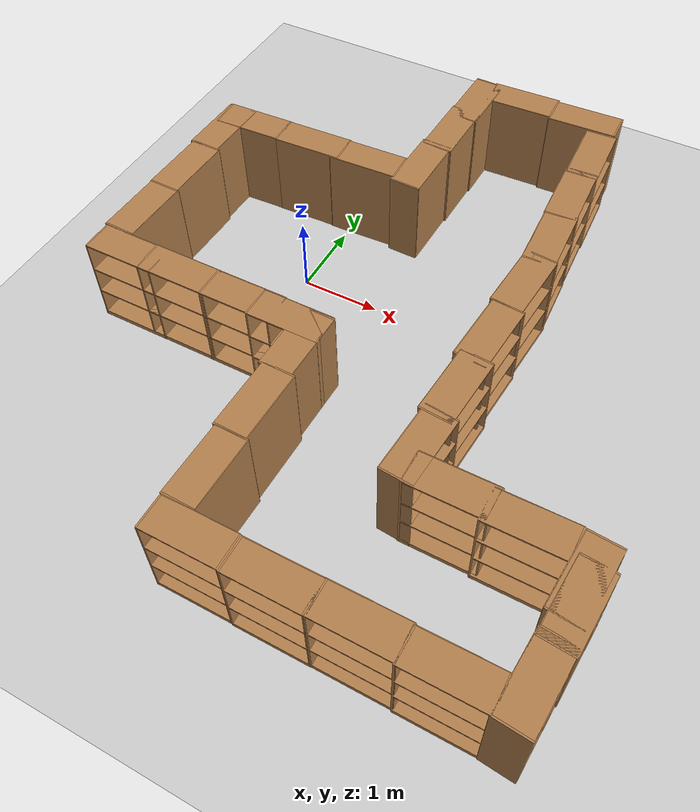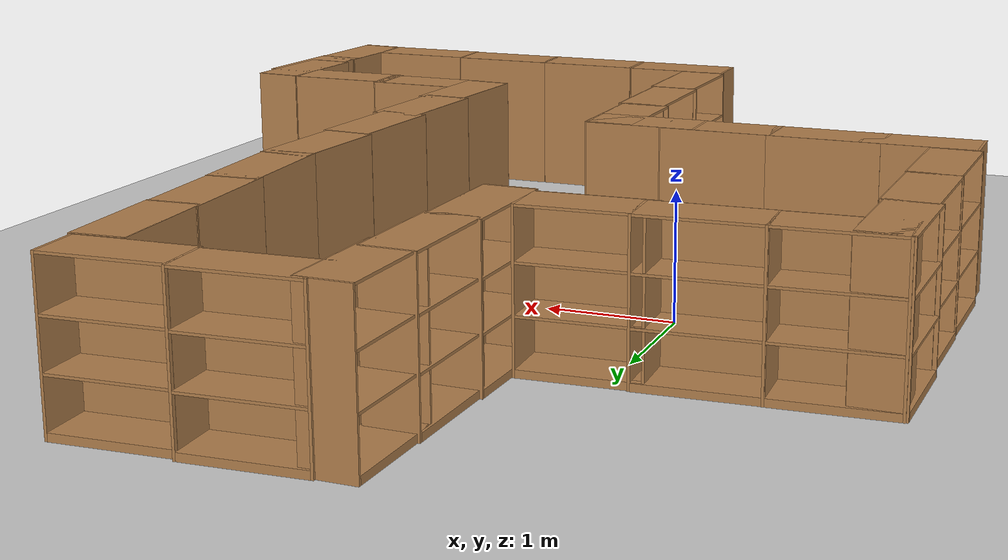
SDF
<sdf version="1.6">
 <world name="default">
  <light name="sun" type="directional">
   <pose>0 0 10 0 -0 0</pose>
   <diffuse>0.8 0.8 0.8 1</diffuse>
   <specular>0.2 0.2 0.2 1</specular>
   <attenuation>
    <range>1000</range>
    <constant>0.9</constant>
    <linear>0.01</linear>
    <quadratic>0.001</quadratic>
   </attenuation>
   <direction>-0.5 0.1 -0.9</direction>
  </light>
  <model name="ground_plane">
   <static>1</static>
   <link name="link">
    <collision name="collision">
     <geometry><plane><normal>0 0 1</normal><size>100 100</size></plane></geometry>
     <surface>
      <contact><collide_bitmask>65535</collide_bitmask></contact>
      <friction><ode><mu>100</mu><mu2>50</mu2></ode></friction>
     </surface>
    </collision>
    <visual name="visual">
     <cast_shadows>0</cast_shadows>
     <geometry><plane><normal>0 0 1</normal><size>100 100</size></plane></geometry>
     <material>
      <script><uri>file://media/materials/scripts/gazebo.material</uri><name>Gazebo/Grey</name></script>
     </material>
    </visual>
   </link>
  </model>
  <gravity>0 0 -9.8</gravity>
  <magnetic_field>6e-06 2.3e-05 -4.2e-05</magnetic_field>
  <atmosphere type="adiabatic"/>
  <physics name="default_physics" default="0" type="ode">
   <max_step_size>0.001</max_step_size>
   <real_time_factor>1</real_time_factor>
   <real_time_update_rate>1000</real_time_update_rate>
  </physics>
  <scene><ambient>0.4 0.4 0.4 1</ambient><background>0.7 0.7 0.7 1</background><shadows>1</shadows></scene>
  <spherical_coordinates>
   <surface_model>EARTH_WGS84</surface_model>
   <latitude_deg>0</latitude_deg>
   <longitude_deg>0</longitude_deg>
   <elevation>0</elevation>
   <heading_deg>0</heading_deg>
  </spherical_coordinates>
  <model name="bookshelf">
   <static>1</static>
   <link name="link">
    <inertial><mass>1</mass></inertial>
    <collision name="back">
     <pose>0 0.005 0.6 0 -0 0</pose>
     <geometry><box><size>0.9 0.01 1.2</size></box></geometry>
    </collision>
    <visual name="visual1">
     <pose>0 0.005 0.6 0 -0 0</pose>
     <geometry><box><size>0.9 0.01 1.2</size></box></geometry>
     <material>
      <script><uri>file://media/materials/scripts/gazebo.material</uri><name>Gazebo/Wood</name></script>
     </material>
    </visual>
    <collision name="left_side">
     <pose>0.45 -0.195 0.6 0 -0 0</pose>
     <geometry><box><size>0.02 0.4 1.2</size></box></geometry>
    </collision>
    <visual name="visual2">
     <pose>0.45 -0.195 0.6 0 -0 0</pose>
     <geometry><box><size>0.02 0.4 1.2</size></box></geometry>
     <material>
      <script><uri>file://media/materials/scripts/gazebo.material</uri><name>Gazebo/Wood</name></script>
     </material>
    </visual>
    <collision name="right_side">
     <pose>-0.45 -0.195 0.6 0 -0 0</pose>
     <geometry><box><size>0.02 0.4 1.2</size></box></geometry>
    </collision>
    <visual name="visual3">
     <pose>-0.45 -0.195 0.6 0 -0 0</pose>
     <geometry><box><size>0.02 0.4 1.2</size></box></geometry>
     <material>
      <script><uri>file://media/materials/scripts/gazebo.material</uri><name>Gazebo/Wood</name></script>
     </material>
    </visual>
    <collision name="bottom">
     <pose>0 -0.195 0.03 0 -0 0</pose>
     <geometry><box><size>0.88 0.4 0.06</size></box></geometry>
    </collision>
    <visual name="visual4">
     <pose>0 -0.195 0.03 0 -0 0</pose>
     <geometry><box><size>0.88 0.4 0.06</size></box></geometry>
     <material>
      <script><uri>file://media/materials/scripts/gazebo.material</uri><name>Gazebo/Wood</name></script>
     </material>
    </visual>
    <collision name="top">
     <pose>0 -0.195 1.19 0 -0 0</pose>
     <geometry><box><size>0.88 0.4 0.02</size></box></geometry>
    </collision>
    <visual name="visual5">
     <pose>0 -0.195 1.19 0 -0 0</pose>
     <geometry><box><size>0.88 0.4 0.02</size></box></geometry>
     <material>
      <script><uri>file://media/materials/scripts/gazebo.material</uri><name>Gazebo/Wood</name></script>
     </material>
    </visual>
    <collision name="low_shelf">
     <pose>0 -0.195 0.43 0 -0 0</pose>
     <geometry><box><size>0.88 0.4 0.02</size></box></geometry>
    </collision>
    <visual name="visual6">
     <pose>0 -0.195 0.43 0 -0 0</pose>
     <geometry><box><size>0.88 0.4 0.02</size></box></geometry>
     <material>
      <script><uri>file://media/materials/scripts/gazebo.material</uri><name>Gazebo/Wood</name></script>
     </material>
    </visual>
    <collision name="high_shelf">
     <pose>0 -0.195 0.8 0 -0 0</pose>
     <geometry><box><size>0.88 0.4 0.02</size></box></geometry>
    </collision>
    <visual name="visual7">
     <pose>0 -0.195 0.8 0 -0 0</pose>
     <geometry><box><size>0.88 0.4 0.02</size></box></geometry>
     <material>
      <script><uri>file://media/materials/scripts/gazebo.material</uri><name>Gazebo/Wood</name></script>
     </material>
    </visual>
   </link>
   <pose>0.085981 -1.25886 0 0 -0 0</pose>
  </model>
  <model name="bookshelf_clone">
   <static>1</static>
   <link name="link">
    <inertial><mass>1</mass></inertial>
    <collision name="back">
     <pose>0 0.005 0.6 0 -0 0</pose>
     <geometry><box><size>0.9 0.01 1.2</size></box></geometry>
    </collision>
    <visual name="visual1">
     <pose>0 0.005 0.6 0 -0 0</pose>
     <geometry><box><size>0.9 0.01 1.2</size></box></geometry>
     <material>
      <script><uri>file://media/materials/scripts/gazebo.material</uri><name>Gazebo/Wood</name></script>
     </material>
    </visual>
    <collision name="left_side">
     <pose>0.45 -0.195 0.6 0 -0 0</pose>
     <geometry><box><size>0.02 0.4 1.2</size></box></geometry>
    </collision>
    <visual name="visual2">
     <pose>0.45 -0.195 0.6 0 -0 0</pose>
     <geometry><box><size>0.02 0.4 1.2</size></box></geometry>
     <material>
      <script><uri>file://media/materials/scripts/gazebo.material</uri><name>Gazebo/Wood</name></script>
     </material>
    </visual>
    <collision name="right_side">
     <pose>-0.45 -0.195 0.6 0 -0 0</pose>
     <geometry><box><size>0.02 0.4 1.2</size></box></geometry>
    </collision>
    <visual name="visual3">
     <pose>-0.45 -0.195 0.6 0 -0 0</pose>
     <geometry><box><size>0.02 0.4 1.2</size></box></geometry>
     <material>
      <script><uri>file://media/materials/scripts/gazebo.material</uri><name>Gazebo/Wood</name></script>
     </material>
    </visual>
    <collision name="bottom">
     <pose>0 -0.195 0.03 0 -0 0</pose>
     <geometry><box><size>0.88 0.4 0.06</size></box></geometry>
    </collision>
    <visual name="visual4">
     <pose>0 -0.195 0.03 0 -0 0</pose>
     <geometry><box><size>0.88 0.4 0.06</size></box></geometry>
     <material>
      <script><uri>file://media/materials/scripts/gazebo.material</uri><name>Gazebo/Wood</name></script>
     </material>
    </visual>
    <collision name="top">
     <pose>0 -0.195 1.19 0 -0 0</pose>
     <geometry><box><size>0.88 0.4 0.02</size></box></geometry>
    </collision>
    <visual name="visual5">
     <pose>0 -0.195 1.19 0 -0 0</pose>
     <geometry><box><size>0.88 0.4 0.02</size></box></geometry>
     <material>
      <script><uri>file://media/materials/scripts/gazebo.material</uri><name>Gazebo/Wood</name></script>
     </material>
    </visual>
    <collision name="low_shelf">
     <pose>0 -0.195 0.43 0 -0 0</pose>
     <geometry><box><size>0.88 0.4 0.02</size></box></geometry>
    </collision>
    <visual name="visual6">
     <pose>0 -0.195 0.43 0 -0 0</pose>
     <geometry><box><size>0.88 0.4 0.02</size></box></geometry>
     <material>
      <script><uri>file://media/materials/scripts/gazebo.material</uri><name>Gazebo/Wood</name></script>
     </material>
    </visual>
    <collision name="high_shelf">
     <pose>0 -0.195 0.8 0 -0 0</pose>
     <geometry><box><size>0.88 0.4 0.02</size></box></geometry>
    </collision>
    <visual name="visual7">
     <pose>0 -0.195 0.8 0 -0 0</pose>
     <geometry><box><size>0.88 0.4 0.02</size></box></geometry>
     <material>
      <script><uri>file://media/materials/scripts/gazebo.material</uri><name>Gazebo/Wood</name></script>
     </material>
    </visual>
   </link>
   <pose>-0.779963 -1.25694 0 0 -0 0</pose>
  </model>
  <model name="bookshelf_clone_0">
   <static>1</static>
   <link name="link">
    <inertial><mass>1</mass></inertial>
    <collision name="back">
     <pose>0 0.005 0.6 0 -0 0</pose>
     <geometry><box><size>0.9 0.01 1.2</size></box></geometry>
    </collision>
    <visual name="visual1">
     <pose>0 0.005 0.6 0 -0 0</pose>
     <geometry><box><size>0.9 0.01 1.2</size></box></geometry>
     <material>
      <script><uri>file://media/materials/scripts/gazebo.material</uri><name>Gazebo/Wood</name></script>
     </material>
    </visual>
    <collision name="left_side">
     <pose>0.45 -0.195 0.6 0 -0 0</pose>
     <geometry><box><size>0.02 0.4 1.2</size></box></geometry>
    </collision>
    <visual name="visual2">
     <pose>0.45 -0.195 0.6 0 -0 0</pose>
     <geometry><box><size>0.02 0.4 1.2</size></box></geometry>
     <material>
      <script><uri>file://media/materials/scripts/gazebo.material</uri><name>Gazebo/Wood</name></script>
     </material>
    </visual>
    <collision name="right_side">
     <pose>-0.45 -0.195 0.6 0 -0 0</pose>
     <geometry><box><size>0.02 0.4 1.2</size></box></geometry>
    </collision>
    <visual name="visual3">
     <pose>-0.45 -0.195 0.6 0 -0 0</pose>
     <geometry><box><size>0.02 0.4 1.2</size></box></geometry>
     <material>
      <script><uri>file://media/materials/scripts/gazebo.material</uri><name>Gazebo/Wood</name></script>
     </material>
    </visual>
    <collision name="bottom">
     <pose>0 -0.195 0.03 0 -0 0</pose>
     <geometry><box><size>0.88 0.4 0.06</size></box></geometry>
    </collision>
    <visual name="visual4">
     <pose>0 -0.195 0.03 0 -0 0</pose>
     <geometry><box><size>0.88 0.4 0.06</size></box></geometry>
     <material>
      <script><uri>file://media/materials/scripts/gazebo.material</uri><name>Gazebo/Wood</name></script>
     </material>
    </visual>
    <collision name="top">
     <pose>0 -0.195 1.19 0 -0 0</pose>
     <geometry><box><size>0.88 0.4 0.02</size></box></geometry>
    </collision>
    <visual name="visual5">
     <pose>0 -0.195 1.19 0 -0 0</pose>
     <geometry><box><size>0.88 0.4 0.02</size></box></geometry>
     <material>
      <script><uri>file://media/materials/scripts/gazebo.material</uri><name>Gazebo/Wood</name></script>
     </material>
    </visual>
    <collision name="low_shelf">
     <pose>0 -0.195 0.43 0 -0 0</pose>
     <geometry><box><size>0.88 0.4 0.02</size></box></geometry>
    </collision>
    <visual name="visual6">
     <pose>0 -0.195 0.43 0 -0 0</pose>
     <geometry><box><size>0.88 0.4 0.02</size></box></geometry>
     <material>
      <script><uri>file://media/materials/scripts/gazebo.material</uri><name>Gazebo/Wood</name></script>
     </material>
    </visual>
    <collision name="high_shelf">
     <pose>0 -0.195 0.8 0 -0 0</pose>
     <geometry><box><size>0.88 0.4 0.02</size></box></geometry>
    </collision>
    <visual name="visual7">
     <pose>0 -0.195 0.8 0 -0 0</pose>
     <geometry><box><size>0.88 0.4 0.02</size></box></geometry>
     <material>
      <script><uri>file://media/materials/scripts/gazebo.material</uri><name>Gazebo/Wood</name></script>
     </material>
    </visual>
   </link>
   <pose>-1.51682 -1.25964 0 0 -0 0</pose>
  </model>
  <model name="bookshelf_clone_1">
   <static>1</static>
   <link name="link">
    <inertial><mass>1</mass></inertial>
    <collision name="back">
     <pose>0 0.005 0.6 0 -0 0</pose>
     <geometry><box><size>0.9 0.01 1.2</size></box></geometry>
    </collision>
    <visual name="visual1">
     <pose>0 0.005 0.6 0 -0 0</pose>
     <geometry><box><size>0.9 0.01 1.2</size></box></geometry>
     <material>
      <script><uri>file://media/materials/scripts/gazebo.material</uri><name>Gazebo/Wood</name></script>
     </material>
    </visual>
    <collision name="left_side">
     <pose>0.45 -0.195 0.6 0 -0 0</pose>
     <geometry><box><size>0.02 0.4 1.2</size></box></geometry>
    </collision>
    <visual name="visual2">
     <pose>0.45 -0.195 0.6 0 -0 0</pose>
     <geometry><box><size>0.02 0.4 1.2</size></box></geometry>
     <material>
      <script><uri>file://media/materials/scripts/gazebo.material</uri><name>Gazebo/Wood</name></script>
     </material>
    </visual>
    <collision name="right_side">
     <pose>-0.45 -0.195 0.6 0 -0 0</pose>
     <geometry><box><size>0.02 0.4 1.2</size></box></geometry>
    </collision>
    <visual name="visual3">
     <pose>-0.45 -0.195 0.6 0 -0 0</pose>
     <geometry><box><size>0.02 0.4 1.2</size></box></geometry>
     <material>
      <script><uri>file://media/materials/scripts/gazebo.material</uri><name>Gazebo/Wood</name></script>
     </material>
    </visual>
    <collision name="bottom">
     <pose>0 -0.195 0.03 0 -0 0</pose>
     <geometry><box><size>0.88 0.4 0.06</size></box></geometry>
    </collision>
    <visual name="visual4">
     <pose>0 -0.195 0.03 0 -0 0</pose>
     <geometry><box><size>0.88 0.4 0.06</size></box></geometry>
     <material>
      <script><uri>file://media/materials/scripts/gazebo.material</uri><name>Gazebo/Wood</name></script>
     </material>
    </visual>
    <collision name="top">
     <pose>0 -0.195 1.19 0 -0 0</pose>
     <geometry><box><size>0.88 0.4 0.02</size></box></geometry>
    </collision>
    <visual name="visual5">
     <pose>0 -0.195 1.19 0 -0 0</pose>
     <geometry><box><size>0.88 0.4 0.02</size></box></geometry>
     <material>
      <script><uri>file://media/materials/scripts/gazebo.material</uri><name>Gazebo/Wood</name></script>
     </material>
    </visual>
    <collision name="low_shelf">
     <pose>0 -0.195 0.43 0 -0 0</pose>
     <geometry><box><size>0.88 0.4 0.02</size></box></geometry>
    </collision>
    <visual name="visual6">
     <pose>0 -0.195 0.43 0 -0 0</pose>
     <geometry><box><size>0.88 0.4 0.02</size></box></geometry>
     <material>
      <script><uri>file://media/materials/scripts/gazebo.material</uri><name>Gazebo/Wood</name></script>
     </material>
    </visual>
    <collision name="high_shelf">
     <pose>0 -0.195 0.8 0 -0 0</pose>
     <geometry><box><size>0.88 0.4 0.02</size></box></geometry>
    </collision>
    <visual name="visual7">
     <pose>0 -0.195 0.8 0 -0 0</pose>
     <geometry><box><size>0.88 0.4 0.02</size></box></geometry>
     <material>
      <script><uri>file://media/materials/scripts/gazebo.material</uri><name>Gazebo/Wood</name></script>
     </material>
    </visual>
   </link>
   <pose>-1.5992 -0.793808 0 0 0 -1.59248</pose>
  </model>
  <model name="bookshelf_clone_1_clone">
   <static>1</static>
   <link name="link">
    <inertial><mass>1</mass></inertial>
    <collision name="back">
     <pose>0 0.005 0.6 0 -0 0</pose>
     <geometry><box><size>0.9 0.01 1.2</size></box></geometry>
    </collision>
    <visual name="visual1">
     <pose>0 0.005 0.6 0 -0 0</pose>
     <geometry><box><size>0.9 0.01 1.2</size></box></geometry>
     <material>
      <script><uri>file://media/materials/scripts/gazebo.material</uri><name>Gazebo/Wood</name></script>
     </material>
    </visual>
    <collision name="left_side">
     <pose>0.45 -0.195 0.6 0 -0 0</pose>
     <geometry><box><size>0.02 0.4 1.2</size></box></geometry>
    </collision>
    <visual name="visual2">
     <pose>0.45 -0.195 0.6 0 -0 0</pose>
     <geometry><box><size>0.02 0.4 1.2</size></box></geometry>
     <material>
      <script><uri>file://media/materials/scripts/gazebo.material</uri><name>Gazebo/Wood</name></script>
     </material>
    </visual>
    <collision name="right_side">
     <pose>-0.45 -0.195 0.6 0 -0 0</pose>
     <geometry><box><size>0.02 0.4 1.2</size></box></geometry>
    </collision>
    <visual name="visual3">
     <pose>-0.45 -0.195 0.6 0 -0 0</pose>
     <geometry><box><size>0.02 0.4 1.2</size></box></geometry>
     <material>
      <script><uri>file://media/materials/scripts/gazebo.material</uri><name>Gazebo/Wood</name></script>
     </material>
    </visual>
    <collision name="bottom">
     <pose>0 -0.195 0.03 0 -0 0</pose>
     <geometry><box><size>0.88 0.4 0.06</size></box></geometry>
    </collision>
    <visual name="visual4">
     <pose>0 -0.195 0.03 0 -0 0</pose>
     <geometry><box><size>0.88 0.4 0.06</size></box></geometry>
     <material>
      <script><uri>file://media/materials/scripts/gazebo.material</uri><name>Gazebo/Wood</name></script>
     </material>
    </visual>
    <collision name="top">
     <pose>0 -0.195 1.19 0 -0 0</pose>
     <geometry><box><size>0.88 0.4 0.02</size></box></geometry>
    </collision>
    <visual name="visual5">
     <pose>0 -0.195 1.19 0 -0 0</pose>
     <geometry><box><size>0.88 0.4 0.02</size></box></geometry>
     <material>
      <script><uri>file://media/materials/scripts/gazebo.material</uri><name>Gazebo/Wood</name></script>
     </material>
    </visual>
    <collision name="low_shelf">
     <pose>0 -0.195 0.43 0 -0 0</pose>
     <geometry><box><size>0.88 0.4 0.02</size></box></geometry>
    </collision>
    <visual name="visual6">
     <pose>0 -0.195 0.43 0 -0 0</pose>
     <geometry><box><size>0.88 0.4 0.02</size></box></geometry>
     <material>
      <script><uri>file://media/materials/scripts/gazebo.material</uri><name>Gazebo/Wood</name></script>
     </material>
    </visual>
    <collision name="high_shelf">
     <pose>0 -0.195 0.8 0 -0 0</pose>
     <geometry><box><size>0.88 0.4 0.02</size></box></geometry>
    </collision>
    <visual name="visual7">
     <pose>0 -0.195 0.8 0 -0 0</pose>
     <geometry><box><size>0.88 0.4 0.02</size></box></geometry>
     <material>
      <script><uri>file://media/materials/scripts/gazebo.material</uri><name>Gazebo/Wood</name></script>
     </material>
    </visual>
   </link>
   <pose>-1.58956 0.092038 0 0 0 -1.59248</pose>
  </model>
  <model name="bookshelf_clone_1_clone_0">
   <static>1</static>
   <link name="link">
    <inertial><mass>1</mass></inertial>
    <collision name="back">
     <pose>0 0.005 0.6 0 -0 0</pose>
     <geometry><box><size>0.9 0.01 1.2</size></box></geometry>
    </collision>
    <visual name="visual1">
     <pose>0 0.005 0.6 0 -0 0</pose>
     <geometry><box><size>0.9 0.01 1.2</size></box></geometry>
     <material>
      <script><uri>file://media/materials/scripts/gazebo.material</uri><name>Gazebo/Wood</name></script>
     </material>
    </visual>
    <collision name="left_side">
     <pose>0.45 -0.195 0.6 0 -0 0</pose>
     <geometry><box><size>0.02 0.4 1.2</size></box></geometry>
    </collision>
    <visual name="visual2">
     <pose>0.45 -0.195 0.6 0 -0 0</pose>
     <geometry><box><size>0.02 0.4 1.2</size></box></geometry>
     <material>
      <script><uri>file://media/materials/scripts/gazebo.material</uri><name>Gazebo/Wood</name></script>
     </material>
    </visual>
    <collision name="right_side">
     <pose>-0.45 -0.195 0.6 0 -0 0</pose>
     <geometry><box><size>0.02 0.4 1.2</size></box></geometry>
    </collision>
    <visual name="visual3">
     <pose>-0.45 -0.195 0.6 0 -0 0</pose>
     <geometry><box><size>0.02 0.4 1.2</size></box></geometry>
     <material>
      <script><uri>file://media/materials/scripts/gazebo.material</uri><name>Gazebo/Wood</name></script>
     </material>
    </visual>
    <collision name="bottom">
     <pose>0 -0.195 0.03 0 -0 0</pose>
     <geometry><box><size>0.88 0.4 0.06</size></box></geometry>
    </collision>
    <visual name="visual4">
     <pose>0 -0.195 0.03 0 -0 0</pose>
     <geometry><box><size>0.88 0.4 0.06</size></box></geometry>
     <material>
      <script><uri>file://media/materials/scripts/gazebo.material</uri><name>Gazebo/Wood</name></script>
     </material>
    </visual>
    <collision name="top">
     <pose>0 -0.195 1.19 0 -0 0</pose>
     <geometry><box><size>0.88 0.4 0.02</size></box></geometry>
    </collision>
    <visual name="visual5">
     <pose>0 -0.195 1.19 0 -0 0</pose>
     <geometry><box><size>0.88 0.4 0.02</size></box></geometry>
     <material>
      <script><uri>file://media/materials/scripts/gazebo.material</uri><name>Gazebo/Wood</name></script>
     </material>
    </visual>
    <collision name="low_shelf">
     <pose>0 -0.195 0.43 0 -0 0</pose>
     <geometry><box><size>0.88 0.4 0.02</size></box></geometry>
    </collision>
    <visual name="visual6">
     <pose>0 -0.195 0.43 0 -0 0</pose>
     <geometry><box><size>0.88 0.4 0.02</size></box></geometry>
     <material>
      <script><uri>file://media/materials/scripts/gazebo.material</uri><name>Gazebo/Wood</name></script>
     </material>
    </visual>
    <collision name="high_shelf">
     <pose>0 -0.195 0.8 0 -0 0</pose>
     <geometry><box><size>0.88 0.4 0.02</size></box></geometry>
    </collision>
    <visual name="visual7">
     <pose>0 -0.195 0.8 0 -0 0</pose>
     <geometry><box><size>0.88 0.4 0.02</size></box></geometry>
     <material>
      <script><uri>file://media/materials/scripts/gazebo.material</uri><name>Gazebo/Wood</name></script>
     </material>
    </visual>
   </link>
   <pose>-1.60052 0.980763 0 0 0 -1.59248</pose>
  </model>
  <model name="bookshelf_clone_0_clone">
   <static>1</static>
   <link name="link">
    <inertial><mass>1</mass></inertial>
    <collision name="back">
     <pose>0 0.005 0.6 0 -0 0</pose>
     <geometry><box><size>0.9 0.01 1.2</size></box></geometry>
    </collision>
    <visual name="visual1">
     <pose>0 0.005 0.6 0 -0 0</pose>
     <geometry><box><size>0.9 0.01 1.2</size></box></geometry>
     <material>
      <script><uri>file://media/materials/scripts/gazebo.material</uri><name>Gazebo/Wood</name></script>
     </material>
    </visual>
    <collision name="left_side">
     <pose>0.45 -0.195 0.6 0 -0 0</pose>
     <geometry><box><size>0.02 0.4 1.2</size></box></geometry>
    </collision>
    <visual name="visual2">
     <pose>0.45 -0.195 0.6 0 -0 0</pose>
     <geometry><box><size>0.02 0.4 1.2</size></box></geometry>
     <material>
      <script><uri>file://media/materials/scripts/gazebo.material</uri><name>Gazebo/Wood</name></script>
     </material>
    </visual>
    <collision name="right_side">
     <pose>-0.45 -0.195 0.6 0 -0 0</pose>
     <geometry><box><size>0.02 0.4 1.2</size></box></geometry>
    </collision>
    <visual name="visual3">
     <pose>-0.45 -0.195 0.6 0 -0 0</pose>
     <geometry><box><size>0.02 0.4 1.2</size></box></geometry>
     <material>
      <script><uri>file://media/materials/scripts/gazebo.material</uri><name>Gazebo/Wood</name></script>
     </material>
    </visual>
    <collision name="bottom">
     <pose>0 -0.195 0.03 0 -0 0</pose>
     <geometry><box><size>0.88 0.4 0.06</size></box></geometry>
    </collision>
    <visual name="visual4">
     <pose>0 -0.195 0.03 0 -0 0</pose>
     <geometry><box><size>0.88 0.4 0.06</size></box></geometry>
     <material>
      <script><uri>file://media/materials/scripts/gazebo.material</uri><name>Gazebo/Wood</name></script>
     </material>
    </visual>
    <collision name="top">
     <pose>0 -0.195 1.19 0 -0 0</pose>
     <geometry><box><size>0.88 0.4 0.02</size></box></geometry>
    </collision>
    <visual name="visual5">
     <pose>0 -0.195 1.19 0 -0 0</pose>
     <geometry><box><size>0.88 0.4 0.02</size></box></geometry>
     <material>
      <script><uri>file://media/materials/scripts/gazebo.material</uri><name>Gazebo/Wood</name></script>
     </material>
    </visual>
    <collision name="low_shelf">
     <pose>0 -0.195 0.43 0 -0 0</pose>
     <geometry><box><size>0.88 0.4 0.02</size></box></geometry>
    </collision>
    <visual name="visual6">
     <pose>0 -0.195 0.43 0 -0 0</pose>
     <geometry><box><size>0.88 0.4 0.02</size></box></geometry>
     <material>
      <script><uri>file://media/materials/scripts/gazebo.material</uri><name>Gazebo/Wood</name></script>
     </material>
    </visual>
    <collision name="high_shelf">
     <pose>0 -0.195 0.8 0 -0 0</pose>
     <geometry><box><size>0.88 0.4 0.02</size></box></geometry>
    </collision>
    <visual name="visual7">
     <pose>0 -0.195 0.8 0 -0 0</pose>
     <geometry><box><size>0.88 0.4 0.02</size></box></geometry>
     <material>
      <script><uri>file://media/materials/scripts/gazebo.material</uri><name>Gazebo/Wood</name></script>
     </material>
    </visual>
   </link>
   <pose>-1.49307 1.07905 0 0 0 -3.10047</pose>
  </model>
  <model name="bookshelf_clone_0_clone_clone">
   <static>1</static>
   <link name="link">
    <inertial><mass>1</mass></inertial>
    <collision name="back">
     <pose>0 0.005 0.6 0 -0 0</pose>
     <geometry><box><size>0.9 0.01 1.2</size></box></geometry>
    </collision>
    <visual name="visual1">
     <pose>0 0.005 0.6 0 -0 0</pose>
     <geometry><box><size>0.9 0.01 1.2</size></box></geometry>
     <material>
      <script><uri>file://media/materials/scripts/gazebo.material</uri><name>Gazebo/Wood</name></script>
     </material>
    </visual>
    <collision name="left_side">
     <pose>0.45 -0.195 0.6 0 -0 0</pose>
     <geometry><box><size>0.02 0.4 1.2</size></box></geometry>
    </collision>
    <visual name="visual2">
     <pose>0.45 -0.195 0.6 0 -0 0</pose>
     <geometry><box><size>0.02 0.4 1.2</size></box></geometry>
     <material>
      <script><uri>file://media/materials/scripts/gazebo.material</uri><name>Gazebo/Wood</name></script>
     </material>
    </visual>
    <collision name="right_side">
     <pose>-0.45 -0.195 0.6 0 -0 0</pose>
     <geometry><box><size>0.02 0.4 1.2</size></box></geometry>
    </collision>
    <visual name="visual3">
     <pose>-0.45 -0.195 0.6 0 -0 0</pose>
     <geometry><box><size>0.02 0.4 1.2</size></box></geometry>
     <material>
      <script><uri>file://media/materials/scripts/gazebo.material</uri><name>Gazebo/Wood</name></script>
     </material>
    </visual>
    <collision name="bottom">
     <pose>0 -0.195 0.03 0 -0 0</pose>
     <geometry><box><size>0.88 0.4 0.06</size></box></geometry>
    </collision>
    <visual name="visual4">
     <pose>0 -0.195 0.03 0 -0 0</pose>
     <geometry><box><size>0.88 0.4 0.06</size></box></geometry>
     <material>
      <script><uri>file://media/materials/scripts/gazebo.material</uri><name>Gazebo/Wood</name></script>
     </material>
    </visual>
    <collision name="top">
     <pose>0 -0.195 1.19 0 -0 0</pose>
     <geometry><box><size>0.88 0.4 0.02</size></box></geometry>
    </collision>
    <visual name="visual5">
     <pose>0 -0.195 1.19 0 -0 0</pose>
     <geometry><box><size>0.88 0.4 0.02</size></box></geometry>
     <material>
      <script><uri>file://media/materials/scripts/gazebo.material</uri><name>Gazebo/Wood</name></script>
     </material>
    </visual>
    <collision name="low_shelf">
     <pose>0 -0.195 0.43 0 -0 0</pose>
     <geometry><box><size>0.88 0.4 0.02</size></box></geometry>
    </collision>
    <visual name="visual6">
     <pose>0 -0.195 0.43 0 -0 0</pose>
     <geometry><box><size>0.88 0.4 0.02</size></box></geometry>
     <material>
      <script><uri>file://media/materials/scripts/gazebo.material</uri><name>Gazebo/Wood</name></script>
     </material>
    </visual>
    <collision name="high_shelf">
     <pose>0 -0.195 0.8 0 -0 0</pose>
     <geometry><box><size>0.88 0.4 0.02</size></box></geometry>
    </collision>
    <visual name="visual7">
     <pose>0 -0.195 0.8 0 -0 0</pose>
     <geometry><box><size>0.88 0.4 0.02</size></box></geometry>
     <material>
      <script><uri>file://media/materials/scripts/gazebo.material</uri><name>Gazebo/Wood</name></script>
     </material>
    </visual>
   </link>
   <pose>-0.599355 1.11109 0 0 0 -3.10047</pose>
  </model>
  <model name="bookshelf_clone_0_clone_clone_0">
   <static>1</static>
   <link name="link">
    <inertial><mass>1</mass></inertial>
    <collision name="back">
     <pose>0 0.005 0.6 0 -0 0</pose>
     <geometry><box><size>0.9 0.01 1.2</size></box></geometry>
    </collision>
    <visual name="visual1">
     <pose>0 0.005 0.6 0 -0 0</pose>
     <geometry><box><size>0.9 0.01 1.2</size></box></geometry>
     <material>
      <script><uri>file://media/materials/scripts/gazebo.material</uri><name>Gazebo/Wood</name></script>
     </material>
    </visual>
    <collision name="left_side">
     <pose>0.45 -0.195 0.6 0 -0 0</pose>
     <geometry><box><size>0.02 0.4 1.2</size></box></geometry>
    </collision>
    <visual name="visual2">
     <pose>0.45 -0.195 0.6 0 -0 0</pose>
     <geometry><box><size>0.02 0.4 1.2</size></box></geometry>
     <material>
      <script><uri>file://media/materials/scripts/gazebo.material</uri><name>Gazebo/Wood</name></script>
     </material>
    </visual>
    <collision name="right_side">
     <pose>-0.45 -0.195 0.6 0 -0 0</pose>
     <geometry><box><size>0.02 0.4 1.2</size></box></geometry>
    </collision>
    <visual name="visual3">
     <pose>-0.45 -0.195 0.6 0 -0 0</pose>
     <geometry><box><size>0.02 0.4 1.2</size></box></geometry>
     <material>
      <script><uri>file://media/materials/scripts/gazebo.material</uri><name>Gazebo/Wood</name></script>
     </material>
    </visual>
    <collision name="bottom">
     <pose>0 -0.195 0.03 0 -0 0</pose>
     <geometry><box><size>0.88 0.4 0.06</size></box></geometry>
    </collision>
    <visual name="visual4">
     <pose>0 -0.195 0.03 0 -0 0</pose>
     <geometry><box><size>0.88 0.4 0.06</size></box></geometry>
     <material>
      <script><uri>file://media/materials/scripts/gazebo.material</uri><name>Gazebo/Wood</name></script>
     </material>
    </visual>
    <collision name="top">
     <pose>0 -0.195 1.19 0 -0 0</pose>
     <geometry><box><size>0.88 0.4 0.02</size></box></geometry>
    </collision>
    <visual name="visual5">
     <pose>0 -0.195 1.19 0 -0 0</pose>
     <geometry><box><size>0.88 0.4 0.02</size></box></geometry>
     <material>
      <script><uri>file://media/materials/scripts/gazebo.material</uri><name>Gazebo/Wood</name></script>
     </material>
    </visual>
    <collision name="low_shelf">
     <pose>0 -0.195 0.43 0 -0 0</pose>
     <geometry><box><size>0.88 0.4 0.02</size></box></geometry>
    </collision>
    <visual name="visual6">
     <pose>0 -0.195 0.43 0 -0 0</pose>
     <geometry><box><size>0.88 0.4 0.02</size></box></geometry>
     <material>
      <script><uri>file://media/materials/scripts/gazebo.material</uri><name>Gazebo/Wood</name></script>
     </material>
    </visual>
    <collision name="high_shelf">
     <pose>0 -0.195 0.8 0 -0 0</pose>
     <geometry><box><size>0.88 0.4 0.02</size></box></geometry>
    </collision>
    <visual name="visual7">
     <pose>0 -0.195 0.8 0 -0 0</pose>
     <geometry><box><size>0.88 0.4 0.02</size></box></geometry>
     <material>
      <script><uri>file://media/materials/scripts/gazebo.material</uri><name>Gazebo/Wood</name></script>
     </material>
    </visual>
   </link>
   <pose>0.20456 1.13017 0 0 0 -3.10047</pose>
  </model>
  <model name="bookshelf_clone_1_clone_0_clone">
   <static>1</static>
   <link name="link">
    <inertial><mass>1</mass></inertial>
    <collision name="back">
     <pose>0 0.005 0.6 0 -0 0</pose>
     <geometry><box><size>0.9 0.01 1.2</size></box></geometry>
    </collision>
    <visual name="visual1">
     <pose>0 0.005 0.6 0 -0 0</pose>
     <geometry><box><size>0.9 0.01 1.2</size></box></geometry>
     <material>
      <script><uri>file://media/materials/scripts/gazebo.material</uri><name>Gazebo/Wood</name></script>
     </material>
    </visual>
    <collision name="left_side">
     <pose>0.45 -0.195 0.6 0 -0 0</pose>
     <geometry><box><size>0.02 0.4 1.2</size></box></geometry>
    </collision>
    <visual name="visual2">
     <pose>0.45 -0.195 0.6 0 -0 0</pose>
     <geometry><box><size>0.02 0.4 1.2</size></box></geometry>
     <material>
      <script><uri>file://media/materials/scripts/gazebo.material</uri><name>Gazebo/Wood</name></script>
     </material>
    </visual>
    <collision name="right_side">
     <pose>-0.45 -0.195 0.6 0 -0 0</pose>
     <geometry><box><size>0.02 0.4 1.2</size></box></geometry>
    </collision>
    <visual name="visual3">
     <pose>-0.45 -0.195 0.6 0 -0 0</pose>
     <geometry><box><size>0.02 0.4 1.2</size></box></geometry>
     <material>
      <script><uri>file://media/materials/scripts/gazebo.material</uri><name>Gazebo/Wood</name></script>
     </material>
    </visual>
    <collision name="bottom">
     <pose>0 -0.195 0.03 0 -0 0</pose>
     <geometry><box><size>0.88 0.4 0.06</size></box></geometry>
    </collision>
    <visual name="visual4">
     <pose>0 -0.195 0.03 0 -0 0</pose>
     <geometry><box><size>0.88 0.4 0.06</size></box></geometry>
     <material>
      <script><uri>file://media/materials/scripts/gazebo.material</uri><name>Gazebo/Wood</name></script>
     </material>
    </visual>
    <collision name="top">
     <pose>0 -0.195 1.19 0 -0 0</pose>
     <geometry><box><size>0.88 0.4 0.02</size></box></geometry>
    </collision>
    <visual name="visual5">
     <pose>0 -0.195 1.19 0 -0 0</pose>
     <geometry><box><size>0.88 0.4 0.02</size></box></geometry>
     <material>
      <script><uri>file://media/materials/scripts/gazebo.material</uri><name>Gazebo/Wood</name></script>
     </material>
    </visual>
    <collision name="low_shelf">
     <pose>0 -0.195 0.43 0 -0 0</pose>
     <geometry><box><size>0.88 0.4 0.02</size></box></geometry>
    </collision>
    <visual name="visual6">
     <pose>0 -0.195 0.43 0 -0 0</pose>
     <geometry><box><size>0.88 0.4 0.02</size></box></geometry>
     <material>
      <script><uri>file://media/materials/scripts/gazebo.material</uri><name>Gazebo/Wood</name></script>
     </material>
    </visual>
    <collision name="high_shelf">
     <pose>0 -0.195 0.8 0 -0 0</pose>
     <geometry><box><size>0.88 0.4 0.02</size></box></geometry>
    </collision>
    <visual name="visual7">
     <pose>0 -0.195 0.8 0 -0 0</pose>
     <geometry><box><size>0.88 0.4 0.02</size></box></geometry>
     <material>
      <script><uri>file://media/materials/scripts/gazebo.material</uri><name>Gazebo/Wood</name></script>
     </material>
    </visual>
   </link>
   <pose>1.04575 1.53142 0 0 0 -1.59248</pose>
  </model>
  <model name="bookshelf_clone_1_clone_0_clone_0">
   <static>1</static>
   <link name="link">
    <inertial><mass>1</mass></inertial>
    <collision name="back">
     <pose>0 0.005 0.6 0 -0 0</pose>
     <geometry><box><size>0.9 0.01 1.2</size></box></geometry>
    </collision>
    <visual name="visual1">
     <pose>0 0.005 0.6 0 -0 0</pose>
     <geometry><box><size>0.9 0.01 1.2</size></box></geometry>
     <material>
      <script><uri>file://media/materials/scripts/gazebo.material</uri><name>Gazebo/Wood</name></script>
     </material>
    </visual>
    <collision name="left_side">
     <pose>0.45 -0.195 0.6 0 -0 0</pose>
     <geometry><box><size>0.02 0.4 1.2</size></box></geometry>
    </collision>
    <visual name="visual2">
     <pose>0.45 -0.195 0.6 0 -0 0</pose>
     <geometry><box><size>0.02 0.4 1.2</size></box></geometry>
     <material>
      <script><uri>file://media/materials/scripts/gazebo.material</uri><name>Gazebo/Wood</name></script>
     </material>
    </visual>
    <collision name="right_side">
     <pose>-0.45 -0.195 0.6 0 -0 0</pose>
     <geometry><box><size>0.02 0.4 1.2</size></box></geometry>
    </collision>
    <visual name="visual3">
     <pose>-0.45 -0.195 0.6 0 -0 0</pose>
     <geometry><box><size>0.02 0.4 1.2</size></box></geometry>
     <material>
      <script><uri>file://media/materials/scripts/gazebo.material</uri><name>Gazebo/Wood</name></script>
     </material>
    </visual>
    <collision name="bottom">
     <pose>0 -0.195 0.03 0 -0 0</pose>
     <geometry><box><size>0.88 0.4 0.06</size></box></geometry>
    </collision>
    <visual name="visual4">
     <pose>0 -0.195 0.03 0 -0 0</pose>
     <geometry><box><size>0.88 0.4 0.06</size></box></geometry>
     <material>
      <script><uri>file://media/materials/scripts/gazebo.material</uri><name>Gazebo/Wood</name></script>
     </material>
    </visual>
    <collision name="top">
     <pose>0 -0.195 1.19 0 -0 0</pose>
     <geometry><box><size>0.88 0.4 0.02</size></box></geometry>
    </collision>
    <visual name="visual5">
     <pose>0 -0.195 1.19 0 -0 0</pose>
     <geometry><box><size>0.88 0.4 0.02</size></box></geometry>
     <material>
      <script><uri>file://media/materials/scripts/gazebo.material</uri><name>Gazebo/Wood</name></script>
     </material>
    </visual>
    <collision name="low_shelf">
     <pose>0 -0.195 0.43 0 -0 0</pose>
     <geometry><box><size>0.88 0.4 0.02</size></box></geometry>
    </collision>
    <visual name="visual6">
     <pose>0 -0.195 0.43 0 -0 0</pose>
     <geometry><box><size>0.88 0.4 0.02</size></box></geometry>
     <material>
      <script><uri>file://media/materials/scripts/gazebo.material</uri><name>Gazebo/Wood</name></script>
     </material>
    </visual>
    <collision name="high_shelf">
     <pose>0 -0.195 0.8 0 -0 0</pose>
     <geometry><box><size>0.88 0.4 0.02</size></box></geometry>
    </collision>
    <visual name="visual7">
     <pose>0 -0.195 0.8 0 -0 0</pose>
     <geometry><box><size>0.88 0.4 0.02</size></box></geometry>
     <material>
      <script><uri>file://media/materials/scripts/gazebo.material</uri><name>Gazebo/Wood</name></script>
     </material>
    </visual>
   </link>
   <pose>1.08658 2.37283 0 0 0 -1.59248</pose>
  </model>
  <model name="bookshelf_clone_1_clone_0_clone_1">
   <static>1</static>
   <link name="link">
    <inertial><mass>1</mass></inertial>
    <collision name="back">
     <pose>0 0.005 0.6 0 -0 0</pose>
     <geometry><box><size>0.9 0.01 1.2</size></box></geometry>
    </collision>
    <visual name="visual1">
     <pose>0 0.005 0.6 0 -0 0</pose>
     <geometry><box><size>0.9 0.01 1.2</size></box></geometry>
     <material>
      <script><uri>file://media/materials/scripts/gazebo.material</uri><name>Gazebo/Wood</name></script>
     </material>
    </visual>
    <collision name="left_side">
     <pose>0.45 -0.195 0.6 0 -0 0</pose>
     <geometry><box><size>0.02 0.4 1.2</size></box></geometry>
    </collision>
    <visual name="visual2">
     <pose>0.45 -0.195 0.6 0 -0 0</pose>
     <geometry><box><size>0.02 0.4 1.2</size></box></geometry>
     <material>
      <script><uri>file://media/materials/scripts/gazebo.material</uri><name>Gazebo/Wood</name></script>
     </material>
    </visual>
    <collision name="right_side">
     <pose>-0.45 -0.195 0.6 0 -0 0</pose>
     <geometry><box><size>0.02 0.4 1.2</size></box></geometry>
    </collision>
    <visual name="visual3">
     <pose>-0.45 -0.195 0.6 0 -0 0</pose>
     <geometry><box><size>0.02 0.4 1.2</size></box></geometry>
     <material>
      <script><uri>file://media/materials/scripts/gazebo.material</uri><name>Gazebo/Wood</name></script>
     </material>
    </visual>
    <collision name="bottom">
     <pose>0 -0.195 0.03 0 -0 0</pose>
     <geometry><box><size>0.88 0.4 0.06</size></box></geometry>
    </collision>
    <visual name="visual4">
     <pose>0 -0.195 0.03 0 -0 0</pose>
     <geometry><box><size>0.88 0.4 0.06</size></box></geometry>
     <material>
      <script><uri>file://media/materials/scripts/gazebo.material</uri><name>Gazebo/Wood</name></script>
     </material>
    </visual>
    <collision name="top">
     <pose>0 -0.195 1.19 0 -0 0</pose>
     <geometry><box><size>0.88 0.4 0.02</size></box></geometry>
    </collision>
    <visual name="visual5">
     <pose>0 -0.195 1.19 0 -0 0</pose>
     <geometry><box><size>0.88 0.4 0.02</size></box></geometry>
     <material>
      <script><uri>file://media/materials/scripts/gazebo.material</uri><name>Gazebo/Wood</name></script>
     </material>
    </visual>
    <collision name="low_shelf">
     <pose>0 -0.195 0.43 0 -0 0</pose>
     <geometry><box><size>0.88 0.4 0.02</size></box></geometry>
    </collision>
    <visual name="visual6">
     <pose>0 -0.195 0.43 0 -0 0</pose>
     <geometry><box><size>0.88 0.4 0.02</size></box></geometry>
     <material>
      <script><uri>file://media/materials/scripts/gazebo.material</uri><name>Gazebo/Wood</name></script>
     </material>
    </visual>
    <collision name="high_shelf">
     <pose>0 -0.195 0.8 0 -0 0</pose>
     <geometry><box><size>0.88 0.4 0.02</size></box></geometry>
    </collision>
    <visual name="visual7">
     <pose>0 -0.195 0.8 0 -0 0</pose>
     <geometry><box><size>0.88 0.4 0.02</size></box></geometry>
     <material>
      <script><uri>file://media/materials/scripts/gazebo.material</uri><name>Gazebo/Wood</name></script>
     </material>
    </visual>
   </link>
   <pose>1.11947 3.09609 0 0 0 -1.59248</pose>
  </model>
  <model name="bookshelf_clone_0_clone_clone_1_clone">
   <static>1</static>
   <link name="link">
    <inertial><mass>1</mass></inertial>
    <collision name="back">
     <pose>0 0.005 0.6 0 -0 0</pose>
     <geometry><box><size>0.9 0.01 1.2</size></box></geometry>
    </collision>
    <visual name="visual1">
     <pose>0 0.005 0.6 0 -0 0</pose>
     <geometry><box><size>0.9 0.01 1.2</size></box></geometry>
     <material>
      <script><uri>file://media/materials/scripts/gazebo.material</uri><name>Gazebo/Wood</name></script>
     </material>
    </visual>
    <collision name="left_side">
     <pose>0.45 -0.195 0.6 0 -0 0</pose>
     <geometry><box><size>0.02 0.4 1.2</size></box></geometry>
    </collision>
    <visual name="visual2">
     <pose>0.45 -0.195 0.6 0 -0 0</pose>
     <geometry><box><size>0.02 0.4 1.2</size></box></geometry>
     <material>
      <script><uri>file://media/materials/scripts/gazebo.material</uri><name>Gazebo/Wood</name></script>
     </material>
    </visual>
    <collision name="right_side">
     <pose>-0.45 -0.195 0.6 0 -0 0</pose>
     <geometry><box><size>0.02 0.4 1.2</size></box></geometry>
    </collision>
    <visual name="visual3">
     <pose>-0.45 -0.195 0.6 0 -0 0</pose>
     <geometry><box><size>0.02 0.4 1.2</size></box></geometry>
     <material>
      <script><uri>file://media/materials/scripts/gazebo.material</uri><name>Gazebo/Wood</name></script>
     </material>
    </visual>
    <collision name="bottom">
     <pose>0 -0.195 0.03 0 -0 0</pose>
     <geometry><box><size>0.88 0.4 0.06</size></box></geometry>
    </collision>
    <visual name="visual4">
     <pose>0 -0.195 0.03 0 -0 0</pose>
     <geometry><box><size>0.88 0.4 0.06</size></box></geometry>
     <material>
      <script><uri>file://media/materials/scripts/gazebo.material</uri><name>Gazebo/Wood</name></script>
     </material>
    </visual>
    <collision name="top">
     <pose>0 -0.195 1.19 0 -0 0</pose>
     <geometry><box><size>0.88 0.4 0.02</size></box></geometry>
    </collision>
    <visual name="visual5">
     <pose>0 -0.195 1.19 0 -0 0</pose>
     <geometry><box><size>0.88 0.4 0.02</size></box></geometry>
     <material>
      <script><uri>file://media/materials/scripts/gazebo.material</uri><name>Gazebo/Wood</name></script>
     </material>
    </visual>
    <collision name="low_shelf">
     <pose>0 -0.195 0.43 0 -0 0</pose>
     <geometry><box><size>0.88 0.4 0.02</size></box></geometry>
    </collision>
    <visual name="visual6">
     <pose>0 -0.195 0.43 0 -0 0</pose>
     <geometry><box><size>0.88 0.4 0.02</size></box></geometry>
     <material>
      <script><uri>file://media/materials/scripts/gazebo.material</uri><name>Gazebo/Wood</name></script>
     </material>
    </visual>
    <collision name="high_shelf">
     <pose>0 -0.195 0.8 0 -0 0</pose>
     <geometry><box><size>0.88 0.4 0.02</size></box></geometry>
    </collision>
    <visual name="visual7">
     <pose>0 -0.195 0.8 0 -0 0</pose>
     <geometry><box><size>0.88 0.4 0.02</size></box></geometry>
     <material>
      <script><uri>file://media/materials/scripts/gazebo.material</uri><name>Gazebo/Wood</name></script>
     </material>
    </visual>
   </link>
   <pose>1.49446 3.20129 0 0 0 -3.10047</pose>
  </model>
  <model name="bookshelf_clone_0_clone_clone_1_clone_0">
   <static>1</static>
   <link name="link">
    <inertial><mass>1</mass></inertial>
    <collision name="back">
     <pose>0 0.005 0.6 0 -0 0</pose>
     <geometry><box><size>0.9 0.01 1.2</size></box></geometry>
    </collision>
    <visual name="visual1">
     <pose>0 0.005 0.6 0 -0 0</pose>
     <geometry><box><size>0.9 0.01 1.2</size></box></geometry>
     <material>
      <script><uri>file://media/materials/scripts/gazebo.material</uri><name>Gazebo/Wood</name></script>
     </material>
    </visual>
    <collision name="left_side">
     <pose>0.45 -0.195 0.6 0 -0 0</pose>
     <geometry><box><size>0.02 0.4 1.2</size></box></geometry>
    </collision>
    <visual name="visual2">
     <pose>0.45 -0.195 0.6 0 -0 0</pose>
     <geometry><box><size>0.02 0.4 1.2</size></box></geometry>
     <material>
      <script><uri>file://media/materials/scripts/gazebo.material</uri><name>Gazebo/Wood</name></script>
     </material>
    </visual>
    <collision name="right_side">
     <pose>-0.45 -0.195 0.6 0 -0 0</pose>
     <geometry><box><size>0.02 0.4 1.2</size></box></geometry>
    </collision>
    <visual name="visual3">
     <pose>-0.45 -0.195 0.6 0 -0 0</pose>
     <geometry><box><size>0.02 0.4 1.2</size></box></geometry>
     <material>
      <script><uri>file://media/materials/scripts/gazebo.material</uri><name>Gazebo/Wood</name></script>
     </material>
    </visual>
    <collision name="bottom">
     <pose>0 -0.195 0.03 0 -0 0</pose>
     <geometry><box><size>0.88 0.4 0.06</size></box></geometry>
    </collision>
    <visual name="visual4">
     <pose>0 -0.195 0.03 0 -0 0</pose>
     <geometry><box><size>0.88 0.4 0.06</size></box></geometry>
     <material>
      <script><uri>file://media/materials/scripts/gazebo.material</uri><name>Gazebo/Wood</name></script>
     </material>
    </visual>
    <collision name="top">
     <pose>0 -0.195 1.19 0 -0 0</pose>
     <geometry><box><size>0.88 0.4 0.02</size></box></geometry>
    </collision>
    <visual name="visual5">
     <pose>0 -0.195 1.19 0 -0 0</pose>
     <geometry><box><size>0.88 0.4 0.02</size></box></geometry>
     <material>
      <script><uri>file://media/materials/scripts/gazebo.material</uri><name>Gazebo/Wood</name></script>
     </material>
    </visual>
    <collision name="low_shelf">
     <pose>0 -0.195 0.43 0 -0 0</pose>
     <geometry><box><size>0.88 0.4 0.02</size></box></geometry>
    </collision>
    <visual name="visual6">
     <pose>0 -0.195 0.43 0 -0 0</pose>
     <geometry><box><size>0.88 0.4 0.02</size></box></geometry>
     <material>
      <script><uri>file://media/materials/scripts/gazebo.material</uri><name>Gazebo/Wood</name></script>
     </material>
    </visual>
    <collision name="high_shelf">
     <pose>0 -0.195 0.8 0 -0 0</pose>
     <geometry><box><size>0.88 0.4 0.02</size></box></geometry>
    </collision>
    <visual name="visual7">
     <pose>0 -0.195 0.8 0 -0 0</pose>
     <geometry><box><size>0.88 0.4 0.02</size></box></geometry>
     <material>
      <script><uri>file://media/materials/scripts/gazebo.material</uri><name>Gazebo/Wood</name></script>
     </material>
    </visual>
   </link>
   <pose>2.3937 3.20747 0 0 0 -3.10047</pose>
  </model>
  <model name="bookshelf_clone_0_clone_clone_1_clone_1">
   <static>1</static>
   <link name="link">
    <inertial><mass>1</mass></inertial>
    <collision name="back">
     <pose>0 0.005 0.6 0 -0 0</pose>
     <geometry><box><size>0.9 0.01 1.2</size></box></geometry>
    </collision>
    <visual name="visual1">
     <pose>0 0.005 0.6 0 -0 0</pose>
     <geometry><box><size>0.9 0.01 1.2</size></box></geometry>
     <material>
      <script><uri>file://media/materials/scripts/gazebo.material</uri><name>Gazebo/Wood</name></script>
     </material>
    </visual>
    <collision name="left_side">
     <pose>0.45 -0.195 0.6 0 -0 0</pose>
     <geometry><box><size>0.02 0.4 1.2</size></box></geometry>
    </collision>
    <visual name="visual2">
     <pose>0.45 -0.195 0.6 0 -0 0</pose>
     <geometry><box><size>0.02 0.4 1.2</size></box></geometry>
     <material>
      <script><uri>file://media/materials/scripts/gazebo.material</uri><name>Gazebo/Wood</name></script>
     </material>
    </visual>
    <collision name="right_side">
     <pose>-0.45 -0.195 0.6 0 -0 0</pose>
     <geometry><box><size>0.02 0.4 1.2</size></box></geometry>
    </collision>
    <visual name="visual3">
     <pose>-0.45 -0.195 0.6 0 -0 0</pose>
     <geometry><box><size>0.02 0.4 1.2</size></box></geometry>
     <material>
      <script><uri>file://media/materials/scripts/gazebo.material</uri><name>Gazebo/Wood</name></script>
     </material>
    </visual>
    <collision name="bottom">
     <pose>0 -0.195 0.03 0 -0 0</pose>
     <geometry><box><size>0.88 0.4 0.06</size></box></geometry>
    </collision>
    <visual name="visual4">
     <pose>0 -0.195 0.03 0 -0 0</pose>
     <geometry><box><size>0.88 0.4 0.06</size></box></geometry>
     <material>
      <script><uri>file://media/materials/scripts/gazebo.material</uri><name>Gazebo/Wood</name></script>
     </material>
    </visual>
    <collision name="top">
     <pose>0 -0.195 1.19 0 -0 0</pose>
     <geometry><box><size>0.88 0.4 0.02</size></box></geometry>
    </collision>
    <visual name="visual5">
     <pose>0 -0.195 1.19 0 -0 0</pose>
     <geometry><box><size>0.88 0.4 0.02</size></box></geometry>
     <material>
      <script><uri>file://media/materials/scripts/gazebo.material</uri><name>Gazebo/Wood</name></script>
     </material>
    </visual>
    <collision name="low_shelf">
     <pose>0 -0.195 0.43 0 -0 0</pose>
     <geometry><box><size>0.88 0.4 0.02</size></box></geometry>
    </collision>
    <visual name="visual6">
     <pose>0 -0.195 0.43 0 -0 0</pose>
     <geometry><box><size>0.88 0.4 0.02</size></box></geometry>
     <material>
      <script><uri>file://media/materials/scripts/gazebo.material</uri><name>Gazebo/Wood</name></script>
     </material>
    </visual>
    <collision name="high_shelf">
     <pose>0 -0.195 0.8 0 -0 0</pose>
     <geometry><box><size>0.88 0.4 0.02</size></box></geometry>
    </collision>
    <visual name="visual7">
     <pose>0 -0.195 0.8 0 -0 0</pose>
     <geometry><box><size>0.88 0.4 0.02</size></box></geometry>
     <material>
      <script><uri>file://media/materials/scripts/gazebo.material</uri><name>Gazebo/Wood</name></script>
     </material>
    </visual>
   </link>
   <pose>2.51523 2.72803 0 0 -0 1.62397</pose>
  </model>
  <model name="bookshelf_clone_0_clone_clone_1_clone_2">
   <static>1</static>
   <link name="link">
    <inertial><mass>1</mass></inertial>
    <collision name="back">
     <pose>0 0.005 0.6 0 -0 0</pose>
     <geometry><box><size>0.9 0.01 1.2</size></box></geometry>
    </collision>
    <visual name="visual1">
     <pose>0 0.005 0.6 0 -0 0</pose>
     <geometry><box><size>0.9 0.01 1.2</size></box></geometry>
     <material>
      <script><uri>file://media/materials/scripts/gazebo.material</uri><name>Gazebo/Wood</name></script>
     </material>
    </visual>
    <collision name="left_side">
     <pose>0.45 -0.195 0.6 0 -0 0</pose>
     <geometry><box><size>0.02 0.4 1.2</size></box></geometry>
    </collision>
    <visual name="visual2">
     <pose>0.45 -0.195 0.6 0 -0 0</pose>
     <geometry><box><size>0.02 0.4 1.2</size></box></geometry>
     <material>
      <script><uri>file://media/materials/scripts/gazebo.material</uri><name>Gazebo/Wood</name></script>
     </material>
    </visual>
    <collision name="right_side">
     <pose>-0.45 -0.195 0.6 0 -0 0</pose>
     <geometry><box><size>0.02 0.4 1.2</size></box></geometry>
    </collision>
    <visual name="visual3">
     <pose>-0.45 -0.195 0.6 0 -0 0</pose>
     <geometry><box><size>0.02 0.4 1.2</size></box></geometry>
     <material>
      <script><uri>file://media/materials/scripts/gazebo.material</uri><name>Gazebo/Wood</name></script>
     </material>
    </visual>
    <collision name="bottom">
     <pose>0 -0.195 0.03 0 -0 0</pose>
     <geometry><box><size>0.88 0.4 0.06</size></box></geometry>
    </collision>
    <visual name="visual4">
     <pose>0 -0.195 0.03 0 -0 0</pose>
     <geometry><box><size>0.88 0.4 0.06</size></box></geometry>
     <material>
      <script><uri>file://media/materials/scripts/gazebo.material</uri><name>Gazebo/Wood</name></script>
     </material>
    </visual>
    <collision name="top">
     <pose>0 -0.195 1.19 0 -0 0</pose>
     <geometry><box><size>0.88 0.4 0.02</size></box></geometry>
    </collision>
    <visual name="visual5">
     <pose>0 -0.195 1.19 0 -0 0</pose>
     <geometry><box><size>0.88 0.4 0.02</size></box></geometry>
     <material>
      <script><uri>file://media/materials/scripts/gazebo.material</uri><name>Gazebo/Wood</name></script>
     </material>
    </visual>
    <collision name="low_shelf">
     <pose>0 -0.195 0.43 0 -0 0</pose>
     <geometry><box><size>0.88 0.4 0.02</size></box></geometry>
    </collision>
    <visual name="visual6">
     <pose>0 -0.195 0.43 0 -0 0</pose>
     <geometry><box><size>0.88 0.4 0.02</size></box></geometry>
     <material>
      <script><uri>file://media/materials/scripts/gazebo.material</uri><name>Gazebo/Wood</name></script>
     </material>
    </visual>
    <collision name="high_shelf">
     <pose>0 -0.195 0.8 0 -0 0</pose>
     <geometry><box><size>0.88 0.4 0.02</size></box></geometry>
    </collision>
    <visual name="visual7">
     <pose>0 -0.195 0.8 0 -0 0</pose>
     <geometry><box><size>0.88 0.4 0.02</size></box></geometry>
     <material>
      <script><uri>file://media/materials/scripts/gazebo.material</uri><name>Gazebo/Wood</name></script>
     </material>
    </visual>
   </link>
   <pose>2.5488 1.88622 0 0 -0 1.62397</pose>
  </model>
  <model name="bookshelf_clone_0_clone_clone_1_clone_3">
   <static>1</static>
   <link name="link">
    <inertial><mass>1</mass></inertial>
    <collision name="back">
     <pose>0 0.005 0.6 0 -0 0</pose>
     <geometry><box><size>0.9 0.01 1.2</size></box></geometry>
    </collision>
    <visual name="visual1">
     <pose>0 0.005 0.6 0 -0 0</pose>
     <geometry><box><size>0.9 0.01 1.2</size></box></geometry>
     <material>
      <script><uri>file://media/materials/scripts/gazebo.material</uri><name>Gazebo/Wood</name></script>
     </material>
    </visual>
    <collision name="left_side">
     <pose>0.45 -0.195 0.6 0 -0 0</pose>
     <geometry><box><size>0.02 0.4 1.2</size></box></geometry>
    </collision>
    <visual name="visual2">
     <pose>0.45 -0.195 0.6 0 -0 0</pose>
     <geometry><box><size>0.02 0.4 1.2</size></box></geometry>
     <material>
      <script><uri>file://media/materials/scripts/gazebo.material</uri><name>Gazebo/Wood</name></script>
     </material>
    </visual>
    <collision name="right_side">
     <pose>-0.45 -0.195 0.6 0 -0 0</pose>
     <geometry><box><size>0.02 0.4 1.2</size></box></geometry>
    </collision>
    <visual name="visual3">
     <pose>-0.45 -0.195 0.6 0 -0 0</pose>
     <geometry><box><size>0.02 0.4 1.2</size></box></geometry>
     <material>
      <script><uri>file://media/materials/scripts/gazebo.material</uri><name>Gazebo/Wood</name></script>
     </material>
    </visual>
    <collision name="bottom">
     <pose>0 -0.195 0.03 0 -0 0</pose>
     <geometry><box><size>0.88 0.4 0.06</size></box></geometry>
    </collision>
    <visual name="visual4">
     <pose>0 -0.195 0.03 0 -0 0</pose>
     <geometry><box><size>0.88 0.4 0.06</size></box></geometry>
     <material>
      <script><uri>file://media/materials/scripts/gazebo.material</uri><name>Gazebo/Wood</name></script>
     </material>
    </visual>
    <collision name="top">
     <pose>0 -0.195 1.19 0 -0 0</pose>
     <geometry><box><size>0.88 0.4 0.02</size></box></geometry>
    </collision>
    <visual name="visual5">
     <pose>0 -0.195 1.19 0 -0 0</pose>
     <geometry><box><size>0.88 0.4 0.02</size></box></geometry>
     <material>
      <script><uri>file://media/materials/scripts/gazebo.material</uri><name>Gazebo/Wood</name></script>
     </material>
    </visual>
    <collision name="low_shelf">
     <pose>0 -0.195 0.43 0 -0 0</pose>
     <geometry><box><size>0.88 0.4 0.02</size></box></geometry>
    </collision>
    <visual name="visual6">
     <pose>0 -0.195 0.43 0 -0 0</pose>
     <geometry><box><size>0.88 0.4 0.02</size></box></geometry>
     <material>
      <script><uri>file://media/materials/scripts/gazebo.material</uri><name>Gazebo/Wood</name></script>
     </material>
    </visual>
    <collision name="high_shelf">
     <pose>0 -0.195 0.8 0 -0 0</pose>
     <geometry><box><size>0.88 0.4 0.02</size></box></geometry>
    </collision>
    <visual name="visual7">
     <pose>0 -0.195 0.8 0 -0 0</pose>
     <geometry><box><size>0.88 0.4 0.02</size></box></geometry>
     <material>
      <script><uri>file://media/materials/scripts/gazebo.material</uri><name>Gazebo/Wood</name></script>
     </material>
    </visual>
   </link>
   <pose>2.60133 1.05247 0 0 -0 1.62397</pose>
  </model>
  <model name="bookshelf_clone_0_clone_clone_1_clone_4">
   <static>1</static>
   <link name="link">
    <inertial><mass>1</mass></inertial>
    <collision name="back">
     <pose>0 0.005 0.6 0 -0 0</pose>
     <geometry><box><size>0.9 0.01 1.2</size></box></geometry>
    </collision>
    <visual name="visual1">
     <pose>0 0.005 0.6 0 -0 0</pose>
     <geometry><box><size>0.9 0.01 1.2</size></box></geometry>
     <material>
      <script><uri>file://media/materials/scripts/gazebo.material</uri><name>Gazebo/Wood</name></script>
     </material>
    </visual>
    <collision name="left_side">
     <pose>0.45 -0.195 0.6 0 -0 0</pose>
     <geometry><box><size>0.02 0.4 1.2</size></box></geometry>
    </collision>
    <visual name="visual2">
     <pose>0.45 -0.195 0.6 0 -0 0</pose>
     <geometry><box><size>0.02 0.4 1.2</size></box></geometry>
     <material>
      <script><uri>file://media/materials/scripts/gazebo.material</uri><name>Gazebo/Wood</name></script>
     </material>
    </visual>
    <collision name="right_side">
     <pose>-0.45 -0.195 0.6 0 -0 0</pose>
     <geometry><box><size>0.02 0.4 1.2</size></box></geometry>
    </collision>
    <visual name="visual3">
     <pose>-0.45 -0.195 0.6 0 -0 0</pose>
     <geometry><box><size>0.02 0.4 1.2</size></box></geometry>
     <material>
      <script><uri>file://media/materials/scripts/gazebo.material</uri><name>Gazebo/Wood</name></script>
     </material>
    </visual>
    <collision name="bottom">
     <pose>0 -0.195 0.03 0 -0 0</pose>
     <geometry><box><size>0.88 0.4 0.06</size></box></geometry>
    </collision>
    <visual name="visual4">
     <pose>0 -0.195 0.03 0 -0 0</pose>
     <geometry><box><size>0.88 0.4 0.06</size></box></geometry>
     <material>
      <script><uri>file://media/materials/scripts/gazebo.material</uri><name>Gazebo/Wood</name></script>
     </material>
    </visual>
    <collision name="top">
     <pose>0 -0.195 1.19 0 -0 0</pose>
     <geometry><box><size>0.88 0.4 0.02</size></box></geometry>
    </collision>
    <visual name="visual5">
     <pose>0 -0.195 1.19 0 -0 0</pose>
     <geometry><box><size>0.88 0.4 0.02</size></box></geometry>
     <material>
      <script><uri>file://media/materials/scripts/gazebo.material</uri><name>Gazebo/Wood</name></script>
     </material>
    </visual>
    <collision name="low_shelf">
     <pose>0 -0.195 0.43 0 -0 0</pose>
     <geometry><box><size>0.88 0.4 0.02</size></box></geometry>
    </collision>
    <visual name="visual6">
     <pose>0 -0.195 0.43 0 -0 0</pose>
     <geometry><box><size>0.88 0.4 0.02</size></box></geometry>
     <material>
      <script><uri>file://media/materials/scripts/gazebo.material</uri><name>Gazebo/Wood</name></script>
     </material>
    </visual>
    <collision name="high_shelf">
     <pose>0 -0.195 0.8 0 -0 0</pose>
     <geometry><box><size>0.88 0.4 0.02</size></box></geometry>
    </collision>
    <visual name="visual7">
     <pose>0 -0.195 0.8 0 -0 0</pose>
     <geometry><box><size>0.88 0.4 0.02</size></box></geometry>
     <material>
      <script><uri>file://media/materials/scripts/gazebo.material</uri><name>Gazebo/Wood</name></script>
     </material>
    </visual>
   </link>
   <pose>2.59947 0.264518 0 0 -0 1.49339</pose>
  </model>
  <model name="bookshelf_clone_2">
   <static>1</static>
   <link name="link">
    <inertial><mass>1</mass></inertial>
    <collision name="back">
     <pose>0 0.005 0.6 0 -0 0</pose>
     <geometry><box><size>0.9 0.01 1.2</size></box></geometry>
    </collision>
    <visual name="visual1">
     <pose>0 0.005 0.6 0 -0 0</pose>
     <geometry><box><size>0.9 0.01 1.2</size></box></geometry>
     <material>
      <script><uri>file://media/materials/scripts/gazebo.material</uri><name>Gazebo/Wood</name></script>
     </material>
    </visual>
    <collision name="left_side">
     <pose>0.45 -0.195 0.6 0 -0 0</pose>
     <geometry><box><size>0.02 0.4 1.2</size></box></geometry>
    </collision>
    <visual name="visual2">
     <pose>0.45 -0.195 0.6 0 -0 0</pose>
     <geometry><box><size>0.02 0.4 1.2</size></box></geometry>
     <material>
      <script><uri>file://media/materials/scripts/gazebo.material</uri><name>Gazebo/Wood</name></script>
     </material>
    </visual>
    <collision name="right_side">
     <pose>-0.45 -0.195 0.6 0 -0 0</pose>
     <geometry><box><size>0.02 0.4 1.2</size></box></geometry>
    </collision>
    <visual name="visual3">
     <pose>-0.45 -0.195 0.6 0 -0 0</pose>
     <geometry><box><size>0.02 0.4 1.2</size></box></geometry>
     <material>
      <script><uri>file://media/materials/scripts/gazebo.material</uri><name>Gazebo/Wood</name></script>
     </material>
    </visual>
    <collision name="bottom">
     <pose>0 -0.195 0.03 0 -0 0</pose>
     <geometry><box><size>0.88 0.4 0.06</size></box></geometry>
    </collision>
    <visual name="visual4">
     <pose>0 -0.195 0.03 0 -0 0</pose>
     <geometry><box><size>0.88 0.4 0.06</size></box></geometry>
     <material>
      <script><uri>file://media/materials/scripts/gazebo.material</uri><name>Gazebo/Wood</name></script>
     </material>
    </visual>
    <collision name="top">
     <pose>0 -0.195 1.19 0 -0 0</pose>
     <geometry><box><size>0.88 0.4 0.02</size></box></geometry>
    </collision>
    <visual name="visual5">
     <pose>0 -0.195 1.19 0 -0 0</pose>
     <geometry><box><size>0.88 0.4 0.02</size></box></geometry>
     <material>
      <script><uri>file://media/materials/scripts/gazebo.material</uri><name>Gazebo/Wood</name></script>
     </material>
    </visual>
    <collision name="low_shelf">
     <pose>0 -0.195 0.43 0 -0 0</pose>
     <geometry><box><size>0.88 0.4 0.02</size></box></geometry>
    </collision>
    <visual name="visual6">
     <pose>0 -0.195 0.43 0 -0 0</pose>
     <geometry><box><size>0.88 0.4 0.02</size></box></geometry>
     <material>
      <script><uri>file://media/materials/scripts/gazebo.material</uri><name>Gazebo/Wood</name></script>
     </material>
    </visual>
    <collision name="high_shelf">
     <pose>0 -0.195 0.8 0 -0 0</pose>
     <geometry><box><size>0.88 0.4 0.02</size></box></geometry>
    </collision>
    <visual name="visual7">
     <pose>0 -0.195 0.8 0 -0 0</pose>
     <geometry><box><size>0.88 0.4 0.02</size></box></geometry>
     <material>
      <script><uri>file://media/materials/scripts/gazebo.material</uri><name>Gazebo/Wood</name></script>
     </material>
    </visual>
   </link>
   <pose>0.718513 -1.26879 0 0 -0 0</pose>
  </model>
  <model name="bookshelf_clone_1_clone_0_clone_clone">
   <static>1</static>
   <link name="link">
    <inertial><mass>1</mass></inertial>
    <collision name="back">
     <pose>0 0.005 0.6 0 -0 0</pose>
     <geometry><box><size>0.9 0.01 1.2</size></box></geometry>
    </collision>
    <visual name="visual1">
     <pose>0 0.005 0.6 0 -0 0</pose>
     <geometry><box><size>0.9 0.01 1.2</size></box></geometry>
     <material>
      <script><uri>file://media/materials/scripts/gazebo.material</uri><name>Gazebo/Wood</name></script>
     </material>
    </visual>
    <collision name="left_side">
     <pose>0.45 -0.195 0.6 0 -0 0</pose>
     <geometry><box><size>0.02 0.4 1.2</size></box></geometry>
    </collision>
    <visual name="visual2">
     <pose>0.45 -0.195 0.6 0 -0 0</pose>
     <geometry><box><size>0.02 0.4 1.2</size></box></geometry>
     <material>
      <script><uri>file://media/materials/scripts/gazebo.material</uri><name>Gazebo/Wood</name></script>
     </material>
    </visual>
    <collision name="right_side">
     <pose>-0.45 -0.195 0.6 0 -0 0</pose>
     <geometry><box><size>0.02 0.4 1.2</size></box></geometry>
    </collision>
    <visual name="visual3">
     <pose>-0.45 -0.195 0.6 0 -0 0</pose>
     <geometry><box><size>0.02 0.4 1.2</size></box></geometry>
     <material>
      <script><uri>file://media/materials/scripts/gazebo.material</uri><name>Gazebo/Wood</name></script>
     </material>
    </visual>
    <collision name="bottom">
     <pose>0 -0.195 0.03 0 -0 0</pose>
     <geometry><box><size>0.88 0.4 0.06</size></box></geometry>
    </collision>
    <visual name="visual4">
     <pose>0 -0.195 0.03 0 -0 0</pose>
     <geometry><box><size>0.88 0.4 0.06</size></box></geometry>
     <material>
      <script><uri>file://media/materials/scripts/gazebo.material</uri><name>Gazebo/Wood</name></script>
     </material>
    </visual>
    <collision name="top">
     <pose>0 -0.195 1.19 0 -0 0</pose>
     <geometry><box><size>0.88 0.4 0.02</size></box></geometry>
    </collision>
    <visual name="visual5">
     <pose>0 -0.195 1.19 0 -0 0</pose>
     <geometry><box><size>0.88 0.4 0.02</size></box></geometry>
     <material>
      <script><uri>file://media/materials/scripts/gazebo.material</uri><name>Gazebo/Wood</name></script>
     </material>
    </visual>
    <collision name="low_shelf">
     <pose>0 -0.195 0.43 0 -0 0</pose>
     <geometry><box><size>0.88 0.4 0.02</size></box></geometry>
    </collision>
    <visual name="visual6">
     <pose>0 -0.195 0.43 0 -0 0</pose>
     <geometry><box><size>0.88 0.4 0.02</size></box></geometry>
     <material>
      <script><uri>file://media/materials/scripts/gazebo.material</uri><name>Gazebo/Wood</name></script>
     </material>
    </visual>
    <collision name="high_shelf">
     <pose>0 -0.195 0.8 0 -0 0</pose>
     <geometry><box><size>0.88 0.4 0.02</size></box></geometry>
    </collision>
    <visual name="visual7">
     <pose>0 -0.195 0.8 0 -0 0</pose>
     <geometry><box><size>0.88 0.4 0.02</size></box></geometry>
     <material>
      <script><uri>file://media/materials/scripts/gazebo.material</uri><name>Gazebo/Wood</name></script>
     </material>
    </visual>
   </link>
   <pose>1.16566 -1.73137 0 0 0 -1.59248</pose>
  </model>
  <model name="bookshelf_clone_1_clone_0_clone_clone_clone">
   <static>1</static>
   <link name="link">
    <inertial><mass>1</mass></inertial>
    <collision name="back">
     <pose>0 0.005 0.6 0 -0 0</pose>
     <geometry><box><size>0.9 0.01 1.2</size></box></geometry>
    </collision>
    <visual name="visual1">
     <pose>0 0.005 0.6 0 -0 0</pose>
     <geometry><box><size>0.9 0.01 1.2</size></box></geometry>
     <material>
      <script><uri>file://media/materials/scripts/gazebo.material</uri><name>Gazebo/Wood</name></script>
     </material>
    </visual>
    <collision name="left_side">
     <pose>0.45 -0.195 0.6 0 -0 0</pose>
     <geometry><box><size>0.02 0.4 1.2</size></box></geometry>
    </collision>
    <visual name="visual2">
     <pose>0.45 -0.195 0.6 0 -0 0</pose>
     <geometry><box><size>0.02 0.4 1.2</size></box></geometry>
     <material>
      <script><uri>file://media/materials/scripts/gazebo.material</uri><name>Gazebo/Wood</name></script>
     </material>
    </visual>
    <collision name="right_side">
     <pose>-0.45 -0.195 0.6 0 -0 0</pose>
     <geometry><box><size>0.02 0.4 1.2</size></box></geometry>
    </collision>
    <visual name="visual3">
     <pose>-0.45 -0.195 0.6 0 -0 0</pose>
     <geometry><box><size>0.02 0.4 1.2</size></box></geometry>
     <material>
      <script><uri>file://media/materials/scripts/gazebo.material</uri><name>Gazebo/Wood</name></script>
     </material>
    </visual>
    <collision name="bottom">
     <pose>0 -0.195 0.03 0 -0 0</pose>
     <geometry><box><size>0.88 0.4 0.06</size></box></geometry>
    </collision>
    <visual name="visual4">
     <pose>0 -0.195 0.03 0 -0 0</pose>
     <geometry><box><size>0.88 0.4 0.06</size></box></geometry>
     <material>
      <script><uri>file://media/materials/scripts/gazebo.material</uri><name>Gazebo/Wood</name></script>
     </material>
    </visual>
    <collision name="top">
     <pose>0 -0.195 1.19 0 -0 0</pose>
     <geometry><box><size>0.88 0.4 0.02</size></box></geometry>
    </collision>
    <visual name="visual5">
     <pose>0 -0.195 1.19 0 -0 0</pose>
     <geometry><box><size>0.88 0.4 0.02</size></box></geometry>
     <material>
      <script><uri>file://media/materials/scripts/gazebo.material</uri><name>Gazebo/Wood</name></script>
     </material>
    </visual>
    <collision name="low_shelf">
     <pose>0 -0.195 0.43 0 -0 0</pose>
     <geometry><box><size>0.88 0.4 0.02</size></box></geometry>
    </collision>
    <visual name="visual6">
     <pose>0 -0.195 0.43 0 -0 0</pose>
     <geometry><box><size>0.88 0.4 0.02</size></box></geometry>
     <material>
      <script><uri>file://media/materials/scripts/gazebo.material</uri><name>Gazebo/Wood</name></script>
     </material>
    </visual>
    <collision name="high_shelf">
     <pose>0 -0.195 0.8 0 -0 0</pose>
     <geometry><box><size>0.88 0.4 0.02</size></box></geometry>
    </collision>
    <visual name="visual7">
     <pose>0 -0.195 0.8 0 -0 0</pose>
     <geometry><box><size>0.88 0.4 0.02</size></box></geometry>
     <material>
      <script><uri>file://media/materials/scripts/gazebo.material</uri><name>Gazebo/Wood</name></script>
     </material>
    </visual>
   </link>
   <pose>1.18486 -2.61264 0 0 0 -1.59248</pose>
  </model>
  <model name="bookshelf_clone_1_clone_0_clone_clone_clone_0">
   <static>1</static>
   <link name="link">
    <inertial><mass>1</mass></inertial>
    <collision name="back">
     <pose>0 0.005 0.6 0 -0 0</pose>
     <geometry><box><size>0.9 0.01 1.2</size></box></geometry>
    </collision>
    <visual name="visual1">
     <pose>0 0.005 0.6 0 -0 0</pose>
     <geometry><box><size>0.9 0.01 1.2</size></box></geometry>
     <material>
      <script><uri>file://media/materials/scripts/gazebo.material</uri><name>Gazebo/Wood</name></script>
     </material>
    </visual>
    <collision name="left_side">
     <pose>0.45 -0.195 0.6 0 -0 0</pose>
     <geometry><box><size>0.02 0.4 1.2</size></box></geometry>
    </collision>
    <visual name="visual2">
     <pose>0.45 -0.195 0.6 0 -0 0</pose>
     <geometry><box><size>0.02 0.4 1.2</size></box></geometry>
     <material>
      <script><uri>file://media/materials/scripts/gazebo.material</uri><name>Gazebo/Wood</name></script>
     </material>
    </visual>
    <collision name="right_side">
     <pose>-0.45 -0.195 0.6 0 -0 0</pose>
     <geometry><box><size>0.02 0.4 1.2</size></box></geometry>
    </collision>
    <visual name="visual3">
     <pose>-0.45 -0.195 0.6 0 -0 0</pose>
     <geometry><box><size>0.02 0.4 1.2</size></box></geometry>
     <material>
      <script><uri>file://media/materials/scripts/gazebo.material</uri><name>Gazebo/Wood</name></script>
     </material>
    </visual>
    <collision name="bottom">
     <pose>0 -0.195 0.03 0 -0 0</pose>
     <geometry><box><size>0.88 0.4 0.06</size></box></geometry>
    </collision>
    <visual name="visual4">
     <pose>0 -0.195 0.03 0 -0 0</pose>
     <geometry><box><size>0.88 0.4 0.06</size></box></geometry>
     <material>
      <script><uri>file://media/materials/scripts/gazebo.material</uri><name>Gazebo/Wood</name></script>
     </material>
    </visual>
    <collision name="top">
     <pose>0 -0.195 1.19 0 -0 0</pose>
     <geometry><box><size>0.88 0.4 0.02</size></box></geometry>
    </collision>
    <visual name="visual5">
     <pose>0 -0.195 1.19 0 -0 0</pose>
     <geometry><box><size>0.88 0.4 0.02</size></box></geometry>
     <material>
      <script><uri>file://media/materials/scripts/gazebo.material</uri><name>Gazebo/Wood</name></script>
     </material>
    </visual>
    <collision name="low_shelf">
     <pose>0 -0.195 0.43 0 -0 0</pose>
     <geometry><box><size>0.88 0.4 0.02</size></box></geometry>
    </collision>
    <visual name="visual6">
     <pose>0 -0.195 0.43 0 -0 0</pose>
     <geometry><box><size>0.88 0.4 0.02</size></box></geometry>
     <material>
      <script><uri>file://media/materials/scripts/gazebo.material</uri><name>Gazebo/Wood</name></script>
     </material>
    </visual>
    <collision name="high_shelf">
     <pose>0 -0.195 0.8 0 -0 0</pose>
     <geometry><box><size>0.88 0.4 0.02</size></box></geometry>
    </collision>
    <visual name="visual7">
     <pose>0 -0.195 0.8 0 -0 0</pose>
     <geometry><box><size>0.88 0.4 0.02</size></box></geometry>
     <material>
      <script><uri>file://media/materials/scripts/gazebo.material</uri><name>Gazebo/Wood</name></script>
     </material>
    </visual>
   </link>
   <pose>1.1935 -3.51086 0 0 0 -1.59248</pose>
  </model>
  <model name="bookshelf_clone_0_clone_clone_1_clone_4_clone">
   <static>1</static>
   <link name="link">
    <inertial><mass>1</mass></inertial>
    <collision name="back">
     <pose>0 0.005 0.6 0 -0 0</pose>
     <geometry><box><size>0.9 0.01 1.2</size></box></geometry>
    </collision>
    <visual name="visual1">
     <pose>0 0.005 0.6 0 -0 0</pose>
     <geometry><box><size>0.9 0.01 1.2</size></box></geometry>
     <material>
      <script><uri>file://media/materials/scripts/gazebo.material</uri><name>Gazebo/Wood</name></script>
     </material>
    </visual>
    <collision name="left_side">
     <pose>0.45 -0.195 0.6 0 -0 0</pose>
     <geometry><box><size>0.02 0.4 1.2</size></box></geometry>
    </collision>
    <visual name="visual2">
     <pose>0.45 -0.195 0.6 0 -0 0</pose>
     <geometry><box><size>0.02 0.4 1.2</size></box></geometry>
     <material>
      <script><uri>file://media/materials/scripts/gazebo.material</uri><name>Gazebo/Wood</name></script>
     </material>
    </visual>
    <collision name="right_side">
     <pose>-0.45 -0.195 0.6 0 -0 0</pose>
     <geometry><box><size>0.02 0.4 1.2</size></box></geometry>
    </collision>
    <visual name="visual3">
     <pose>-0.45 -0.195 0.6 0 -0 0</pose>
     <geometry><box><size>0.02 0.4 1.2</size></box></geometry>
     <material>
      <script><uri>file://media/materials/scripts/gazebo.material</uri><name>Gazebo/Wood</name></script>
     </material>
    </visual>
    <collision name="bottom">
     <pose>0 -0.195 0.03 0 -0 0</pose>
     <geometry><box><size>0.88 0.4 0.06</size></box></geometry>
    </collision>
    <visual name="visual4">
     <pose>0 -0.195 0.03 0 -0 0</pose>
     <geometry><box><size>0.88 0.4 0.06</size></box></geometry>
     <material>
      <script><uri>file://media/materials/scripts/gazebo.material</uri><name>Gazebo/Wood</name></script>
     </material>
    </visual>
    <collision name="top">
     <pose>0 -0.195 1.19 0 -0 0</pose>
     <geometry><box><size>0.88 0.4 0.02</size></box></geometry>
    </collision>
    <visual name="visual5">
     <pose>0 -0.195 1.19 0 -0 0</pose>
     <geometry><box><size>0.88 0.4 0.02</size></box></geometry>
     <material>
      <script><uri>file://media/materials/scripts/gazebo.material</uri><name>Gazebo/Wood</name></script>
     </material>
    </visual>
    <collision name="low_shelf">
     <pose>0 -0.195 0.43 0 -0 0</pose>
     <geometry><box><size>0.88 0.4 0.02</size></box></geometry>
    </collision>
    <visual name="visual6">
     <pose>0 -0.195 0.43 0 -0 0</pose>
     <geometry><box><size>0.88 0.4 0.02</size></box></geometry>
     <material>
      <script><uri>file://media/materials/scripts/gazebo.material</uri><name>Gazebo/Wood</name></script>
     </material>
    </visual>
    <collision name="high_shelf">
     <pose>0 -0.195 0.8 0 -0 0</pose>
     <geometry><box><size>0.88 0.4 0.02</size></box></geometry>
    </collision>
    <visual name="visual7">
     <pose>0 -0.195 0.8 0 -0 0</pose>
     <geometry><box><size>0.88 0.4 0.02</size></box></geometry>
     <material>
      <script><uri>file://media/materials/scripts/gazebo.material</uri><name>Gazebo/Wood</name></script>
     </material>
    </visual>
   </link>
   <pose>2.56068 -0.633827 0 0 -0 1.49339</pose>
  </model>
  <model name="bookshelf_clone_0_clone_clone_1_clone_4_clone_0">
   <static>1</static>
   <link name="link">
    <inertial><mass>1</mass></inertial>
    <collision name="back">
     <pose>0 0.005 0.6 0 -0 0</pose>
     <geometry><box><size>0.9 0.01 1.2</size></box></geometry>
    </collision>
    <visual name="visual1">
     <pose>0 0.005 0.6 0 -0 0</pose>
     <geometry><box><size>0.9 0.01 1.2</size></box></geometry>
     <material>
      <script><uri>file://media/materials/scripts/gazebo.material</uri><name>Gazebo/Wood</name></script>
     </material>
    </visual>
    <collision name="left_side">
     <pose>0.45 -0.195 0.6 0 -0 0</pose>
     <geometry><box><size>0.02 0.4 1.2</size></box></geometry>
    </collision>
    <visual name="visual2">
     <pose>0.45 -0.195 0.6 0 -0 0</pose>
     <geometry><box><size>0.02 0.4 1.2</size></box></geometry>
     <material>
      <script><uri>file://media/materials/scripts/gazebo.material</uri><name>Gazebo/Wood</name></script>
     </material>
    </visual>
    <collision name="right_side">
     <pose>-0.45 -0.195 0.6 0 -0 0</pose>
     <geometry><box><size>0.02 0.4 1.2</size></box></geometry>
    </collision>
    <visual name="visual3">
     <pose>-0.45 -0.195 0.6 0 -0 0</pose>
     <geometry><box><size>0.02 0.4 1.2</size></box></geometry>
     <material>
      <script><uri>file://media/materials/scripts/gazebo.material</uri><name>Gazebo/Wood</name></script>
     </material>
    </visual>
    <collision name="bottom">
     <pose>0 -0.195 0.03 0 -0 0</pose>
     <geometry><box><size>0.88 0.4 0.06</size></box></geometry>
    </collision>
    <visual name="visual4">
     <pose>0 -0.195 0.03 0 -0 0</pose>
     <geometry><box><size>0.88 0.4 0.06</size></box></geometry>
     <material>
      <script><uri>file://media/materials/scripts/gazebo.material</uri><name>Gazebo/Wood</name></script>
     </material>
    </visual>
    <collision name="top">
     <pose>0 -0.195 1.19 0 -0 0</pose>
     <geometry><box><size>0.88 0.4 0.02</size></box></geometry>
    </collision>
    <visual name="visual5">
     <pose>0 -0.195 1.19 0 -0 0</pose>
     <geometry><box><size>0.88 0.4 0.02</size></box></geometry>
     <material>
      <script><uri>file://media/materials/scripts/gazebo.material</uri><name>Gazebo/Wood</name></script>
     </material>
    </visual>
    <collision name="low_shelf">
     <pose>0 -0.195 0.43 0 -0 0</pose>
     <geometry><box><size>0.88 0.4 0.02</size></box></geometry>
    </collision>
    <visual name="visual6">
     <pose>0 -0.195 0.43 0 -0 0</pose>
     <geometry><box><size>0.88 0.4 0.02</size></box></geometry>
     <material>
      <script><uri>file://media/materials/scripts/gazebo.material</uri><name>Gazebo/Wood</name></script>
     </material>
    </visual>
    <collision name="high_shelf">
     <pose>0 -0.195 0.8 0 -0 0</pose>
     <geometry><box><size>0.88 0.4 0.02</size></box></geometry>
    </collision>
    <visual name="visual7">
     <pose>0 -0.195 0.8 0 -0 0</pose>
     <geometry><box><size>0.88 0.4 0.02</size></box></geometry>
     <material>
      <script><uri>file://media/materials/scripts/gazebo.material</uri><name>Gazebo/Wood</name></script>
     </material>
    </visual>
   </link>
   <pose>2.54838 -1.45609 0 0 -0 1.49339</pose>
  </model>
  <model name="bookshelf_clone_0_clone_clone_1_clone_4_clone_1">
   <static>1</static>
   <link name="link">
    <inertial><mass>1</mass></inertial>
    <collision name="back">
     <pose>0 0.005 0.6 0 -0 0</pose>
     <geometry><box><size>0.9 0.01 1.2</size></box></geometry>
    </collision>
    <visual name="visual1">
     <pose>0 0.005 0.6 0 -0 0</pose>
     <geometry><box><size>0.9 0.01 1.2</size></box></geometry>
     <material>
      <script><uri>file://media/materials/scripts/gazebo.material</uri><name>Gazebo/Wood</name></script>
     </material>
    </visual>
    <collision name="left_side">
     <pose>0.45 -0.195 0.6 0 -0 0</pose>
     <geometry><box><size>0.02 0.4 1.2</size></box></geometry>
    </collision>
    <visual name="visual2">
     <pose>0.45 -0.195 0.6 0 -0 0</pose>
     <geometry><box><size>0.02 0.4 1.2</size></box></geometry>
     <material>
      <script><uri>file://media/materials/scripts/gazebo.material</uri><name>Gazebo/Wood</name></script>
     </material>
    </visual>
    <collision name="right_side">
     <pose>-0.45 -0.195 0.6 0 -0 0</pose>
     <geometry><box><size>0.02 0.4 1.2</size></box></geometry>
    </collision>
    <visual name="visual3">
     <pose>-0.45 -0.195 0.6 0 -0 0</pose>
     <geometry><box><size>0.02 0.4 1.2</size></box></geometry>
     <material>
      <script><uri>file://media/materials/scripts/gazebo.material</uri><name>Gazebo/Wood</name></script>
     </material>
    </visual>
    <collision name="bottom">
     <pose>0 -0.195 0.03 0 -0 0</pose>
     <geometry><box><size>0.88 0.4 0.06</size></box></geometry>
    </collision>
    <visual name="visual4">
     <pose>0 -0.195 0.03 0 -0 0</pose>
     <geometry><box><size>0.88 0.4 0.06</size></box></geometry>
     <material>
      <script><uri>file://media/materials/scripts/gazebo.material</uri><name>Gazebo/Wood</name></script>
     </material>
    </visual>
    <collision name="top">
     <pose>0 -0.195 1.19 0 -0 0</pose>
     <geometry><box><size>0.88 0.4 0.02</size></box></geometry>
    </collision>
    <visual name="visual5">
     <pose>0 -0.195 1.19 0 -0 0</pose>
     <geometry><box><size>0.88 0.4 0.02</size></box></geometry>
     <material>
      <script><uri>file://media/materials/scripts/gazebo.material</uri><name>Gazebo/Wood</name></script>
     </material>
    </visual>
    <collision name="low_shelf">
     <pose>0 -0.195 0.43 0 -0 0</pose>
     <geometry><box><size>0.88 0.4 0.02</size></box></geometry>
    </collision>
    <visual name="visual6">
     <pose>0 -0.195 0.43 0 -0 0</pose>
     <geometry><box><size>0.88 0.4 0.02</size></box></geometry>
     <material>
      <script><uri>file://media/materials/scripts/gazebo.material</uri><name>Gazebo/Wood</name></script>
     </material>
    </visual>
    <collision name="high_shelf">
     <pose>0 -0.195 0.8 0 -0 0</pose>
     <geometry><box><size>0.88 0.4 0.02</size></box></geometry>
    </collision>
    <visual name="visual7">
     <pose>0 -0.195 0.8 0 -0 0</pose>
     <geometry><box><size>0.88 0.4 0.02</size></box></geometry>
     <material>
      <script><uri>file://media/materials/scripts/gazebo.material</uri><name>Gazebo/Wood</name></script>
     </material>
    </visual>
   </link>
   <pose>2.52468 -2.28787 0 0 -0 1.49339</pose>
  </model>
  <model name="bookshelf_clone_3">
   <static>1</static>
   <link name="link">
    <inertial><mass>1</mass></inertial>
    <collision name="back">
     <pose>0 0.005 0.6 0 -0 0</pose>
     <geometry><box><size>0.9 0.01 1.2</size></box></geometry>
    </collision>
    <visual name="visual1">
     <pose>0 0.005 0.6 0 -0 0</pose>
     <geometry><box><size>0.9 0.01 1.2</size></box></geometry>
     <material>
      <script><uri>file://media/materials/scripts/gazebo.material</uri><name>Gazebo/Wood</name></script>
     </material>
    </visual>
    <collision name="left_side">
     <pose>0.45 -0.195 0.6 0 -0 0</pose>
     <geometry><box><size>0.02 0.4 1.2</size></box></geometry>
    </collision>
    <visual name="visual2">
     <pose>0.45 -0.195 0.6 0 -0 0</pose>
     <geometry><box><size>0.02 0.4 1.2</size></box></geometry>
     <material>
      <script><uri>file://media/materials/scripts/gazebo.material</uri><name>Gazebo/Wood</name></script>
     </material>
    </visual>
    <collision name="right_side">
     <pose>-0.45 -0.195 0.6 0 -0 0</pose>
     <geometry><box><size>0.02 0.4 1.2</size></box></geometry>
    </collision>
    <visual name="visual3">
     <pose>-0.45 -0.195 0.6 0 -0 0</pose>
     <geometry><box><size>0.02 0.4 1.2</size></box></geometry>
     <material>
      <script><uri>file://media/materials/scripts/gazebo.material</uri><name>Gazebo/Wood</name></script>
     </material>
    </visual>
    <collision name="bottom">
     <pose>0 -0.195 0.03 0 -0 0</pose>
     <geometry><box><size>0.88 0.4 0.06</size></box></geometry>
    </collision>
    <visual name="visual4">
     <pose>0 -0.195 0.03 0 -0 0</pose>
     <geometry><box><size>0.88 0.4 0.06</size></box></geometry>
     <material>
      <script><uri>file://media/materials/scripts/gazebo.material</uri><name>Gazebo/Wood</name></script>
     </material>
    </visual>
    <collision name="top">
     <pose>0 -0.195 1.19 0 -0 0</pose>
     <geometry><box><size>0.88 0.4 0.02</size></box></geometry>
    </collision>
    <visual name="visual5">
     <pose>0 -0.195 1.19 0 -0 0</pose>
     <geometry><box><size>0.88 0.4 0.02</size></box></geometry>
     <material>
      <script><uri>file://media/materials/scripts/gazebo.material</uri><name>Gazebo/Wood</name></script>
     </material>
    </visual>
    <collision name="low_shelf">
     <pose>0 -0.195 0.43 0 -0 0</pose>
     <geometry><box><size>0.88 0.4 0.02</size></box></geometry>
    </collision>
    <visual name="visual6">
     <pose>0 -0.195 0.43 0 -0 0</pose>
     <geometry><box><size>0.88 0.4 0.02</size></box></geometry>
     <material>
      <script><uri>file://media/materials/scripts/gazebo.material</uri><name>Gazebo/Wood</name></script>
     </material>
    </visual>
    <collision name="high_shelf">
     <pose>0 -0.195 0.8 0 -0 0</pose>
     <geometry><box><size>0.88 0.4 0.02</size></box></geometry>
    </collision>
    <visual name="visual7">
     <pose>0 -0.195 0.8 0 -0 0</pose>
     <geometry><box><size>0.88 0.4 0.02</size></box></geometry>
     <material>
      <script><uri>file://media/materials/scripts/gazebo.material</uri><name>Gazebo/Wood</name></script>
     </material>
    </visual>
   </link>
   <pose>1.26252 -3.97265 0 0 -0 0</pose>
  </model>
  <model name="bookshelf_clone_4">
   <static>1</static>
   <link name="link">
    <inertial><mass>1</mass></inertial>
    <collision name="back">
     <pose>0 0.005 0.6 0 -0 0</pose>
     <geometry><box><size>0.9 0.01 1.2</size></box></geometry>
    </collision>
    <visual name="visual1">
     <pose>0 0.005 0.6 0 -0 0</pose>
     <geometry><box><size>0.9 0.01 1.2</size></box></geometry>
     <material>
      <script><uri>file://media/materials/scripts/gazebo.material</uri><name>Gazebo/Wood</name></script>
     </material>
    </visual>
    <collision name="left_side">
     <pose>0.45 -0.195 0.6 0 -0 0</pose>
     <geometry><box><size>0.02 0.4 1.2</size></box></geometry>
    </collision>
    <visual name="visual2">
     <pose>0.45 -0.195 0.6 0 -0 0</pose>
     <geometry><box><size>0.02 0.4 1.2</size></box></geometry>
     <material>
      <script><uri>file://media/materials/scripts/gazebo.material</uri><name>Gazebo/Wood</name></script>
     </material>
    </visual>
    <collision name="right_side">
     <pose>-0.45 -0.195 0.6 0 -0 0</pose>
     <geometry><box><size>0.02 0.4 1.2</size></box></geometry>
    </collision>
    <visual name="visual3">
     <pose>-0.45 -0.195 0.6 0 -0 0</pose>
     <geometry><box><size>0.02 0.4 1.2</size></box></geometry>
     <material>
      <script><uri>file://media/materials/scripts/gazebo.material</uri><name>Gazebo/Wood</name></script>
     </material>
    </visual>
    <collision name="bottom">
     <pose>0 -0.195 0.03 0 -0 0</pose>
     <geometry><box><size>0.88 0.4 0.06</size></box></geometry>
    </collision>
    <visual name="visual4">
     <pose>0 -0.195 0.03 0 -0 0</pose>
     <geometry><box><size>0.88 0.4 0.06</size></box></geometry>
     <material>
      <script><uri>file://media/materials/scripts/gazebo.material</uri><name>Gazebo/Wood</name></script>
     </material>
    </visual>
    <collision name="top">
     <pose>0 -0.195 1.19 0 -0 0</pose>
     <geometry><box><size>0.88 0.4 0.02</size></box></geometry>
    </collision>
    <visual name="visual5">
     <pose>0 -0.195 1.19 0 -0 0</pose>
     <geometry><box><size>0.88 0.4 0.02</size></box></geometry>
     <material>
      <script><uri>file://media/materials/scripts/gazebo.material</uri><name>Gazebo/Wood</name></script>
     </material>
    </visual>
    <collision name="low_shelf">
     <pose>0 -0.195 0.43 0 -0 0</pose>
     <geometry><box><size>0.88 0.4 0.02</size></box></geometry>
    </collision>
    <visual name="visual6">
     <pose>0 -0.195 0.43 0 -0 0</pose>
     <geometry><box><size>0.88 0.4 0.02</size></box></geometry>
     <material>
      <script><uri>file://media/materials/scripts/gazebo.material</uri><name>Gazebo/Wood</name></script>
     </material>
    </visual>
    <collision name="high_shelf">
     <pose>0 -0.195 0.8 0 -0 0</pose>
     <geometry><box><size>0.88 0.4 0.02</size></box></geometry>
    </collision>
    <visual name="visual7">
     <pose>0 -0.195 0.8 0 -0 0</pose>
     <geometry><box><size>0.88 0.4 0.02</size></box></geometry>
     <material>
      <script><uri>file://media/materials/scripts/gazebo.material</uri><name>Gazebo/Wood</name></script>
     </material>
    </visual>
   </link>
   <pose>2.18043 -3.98119 0 0 -0 0</pose>
  </model>
  <model name="bookshelf_clone_5">
   <static>1</static>
   <link name="link">
    <inertial><mass>1</mass></inertial>
    <collision name="back">
     <pose>0 0.005 0.6 0 -0 0</pose>
     <geometry><box><size>0.9 0.01 1.2</size></box></geometry>
    </collision>
    <visual name="visual1">
     <pose>0 0.005 0.6 0 -0 0</pose>
     <geometry><box><size>0.9 0.01 1.2</size></box></geometry>
     <material>
      <script><uri>file://media/materials/scripts/gazebo.material</uri><name>Gazebo/Wood</name></script>
     </material>
    </visual>
    <collision name="left_side">
     <pose>0.45 -0.195 0.6 0 -0 0</pose>
     <geometry><box><size>0.02 0.4 1.2</size></box></geometry>
    </collision>
    <visual name="visual2">
     <pose>0.45 -0.195 0.6 0 -0 0</pose>
     <geometry><box><size>0.02 0.4 1.2</size></box></geometry>
     <material>
      <script><uri>file://media/materials/scripts/gazebo.material</uri><name>Gazebo/Wood</name></script>
     </material>
    </visual>
    <collision name="right_side">
     <pose>-0.45 -0.195 0.6 0 -0 0</pose>
     <geometry><box><size>0.02 0.4 1.2</size></box></geometry>
    </collision>
    <visual name="visual3">
     <pose>-0.45 -0.195 0.6 0 -0 0</pose>
     <geometry><box><size>0.02 0.4 1.2</size></box></geometry>
     <material>
      <script><uri>file://media/materials/scripts/gazebo.material</uri><name>Gazebo/Wood</name></script>
     </material>
    </visual>
    <collision name="bottom">
     <pose>0 -0.195 0.03 0 -0 0</pose>
     <geometry><box><size>0.88 0.4 0.06</size></box></geometry>
    </collision>
    <visual name="visual4">
     <pose>0 -0.195 0.03 0 -0 0</pose>
     <geometry><box><size>0.88 0.4 0.06</size></box></geometry>
     <material>
      <script><uri>file://media/materials/scripts/gazebo.material</uri><name>Gazebo/Wood</name></script>
     </material>
    </visual>
    <collision name="top">
     <pose>0 -0.195 1.19 0 -0 0</pose>
     <geometry><box><size>0.88 0.4 0.02</size></box></geometry>
    </collision>
    <visual name="visual5">
     <pose>0 -0.195 1.19 0 -0 0</pose>
     <geometry><box><size>0.88 0.4 0.02</size></box></geometry>
     <material>
      <script><uri>file://media/materials/scripts/gazebo.material</uri><name>Gazebo/Wood</name></script>
     </material>
    </visual>
    <collision name="low_shelf">
     <pose>0 -0.195 0.43 0 -0 0</pose>
     <geometry><box><size>0.88 0.4 0.02</size></box></geometry>
    </collision>
    <visual name="visual6">
     <pose>0 -0.195 0.43 0 -0 0</pose>
     <geometry><box><size>0.88 0.4 0.02</size></box></geometry>
     <material>
      <script><uri>file://media/materials/scripts/gazebo.material</uri><name>Gazebo/Wood</name></script>
     </material>
    </visual>
    <collision name="high_shelf">
     <pose>0 -0.195 0.8 0 -0 0</pose>
     <geometry><box><size>0.88 0.4 0.02</size></box></geometry>
    </collision>
    <visual name="visual7">
     <pose>0 -0.195 0.8 0 -0 0</pose>
     <geometry><box><size>0.88 0.4 0.02</size></box></geometry>
     <material>
      <script><uri>file://media/materials/scripts/gazebo.material</uri><name>Gazebo/Wood</name></script>
     </material>
    </visual>
   </link>
   <pose>3.06264 -3.97725 0 0 -0 0</pose>
  </model>
  <model name="bookshelf_clone_6">
   <static>1</static>
   <link name="link">
    <inertial><mass>1</mass></inertial>
    <collision name="back">
     <pose>0 0.005 0.6 0 -0 0</pose>
     <geometry><box><size>0.9 0.01 1.2</size></box></geometry>
    </collision>
    <visual name="visual1">
     <pose>0 0.005 0.6 0 -0 0</pose>
     <geometry><box><size>0.9 0.01 1.2</size></box></geometry>
     <material>
      <script><uri>file://media/materials/scripts/gazebo.material</uri><name>Gazebo/Wood</name></script>
     </material>
    </visual>
    <collision name="left_side">
     <pose>0.45 -0.195 0.6 0 -0 0</pose>
     <geometry><box><size>0.02 0.4 1.2</size></box></geometry>
    </collision>
    <visual name="visual2">
     <pose>0.45 -0.195 0.6 0 -0 0</pose>
     <geometry><box><size>0.02 0.4 1.2</size></box></geometry>
     <material>
      <script><uri>file://media/materials/scripts/gazebo.material</uri><name>Gazebo/Wood</name></script>
     </material>
    </visual>
    <collision name="right_side">
     <pose>-0.45 -0.195 0.6 0 -0 0</pose>
     <geometry><box><size>0.02 0.4 1.2</size></box></geometry>
    </collision>
    <visual name="visual3">
     <pose>-0.45 -0.195 0.6 0 -0 0</pose>
     <geometry><box><size>0.02 0.4 1.2</size></box></geometry>
     <material>
      <script><uri>file://media/materials/scripts/gazebo.material</uri><name>Gazebo/Wood</name></script>
     </material>
    </visual>
    <collision name="bottom">
     <pose>0 -0.195 0.03 0 -0 0</pose>
     <geometry><box><size>0.88 0.4 0.06</size></box></geometry>
    </collision>
    <visual name="visual4">
     <pose>0 -0.195 0.03 0 -0 0</pose>
     <geometry><box><size>0.88 0.4 0.06</size></box></geometry>
     <material>
      <script><uri>file://media/materials/scripts/gazebo.material</uri><name>Gazebo/Wood</name></script>
     </material>
    </visual>
    <collision name="top">
     <pose>0 -0.195 1.19 0 -0 0</pose>
     <geometry><box><size>0.88 0.4 0.02</size></box></geometry>
    </collision>
    <visual name="visual5">
     <pose>0 -0.195 1.19 0 -0 0</pose>
     <geometry><box><size>0.88 0.4 0.02</size></box></geometry>
     <material>
      <script><uri>file://media/materials/scripts/gazebo.material</uri><name>Gazebo/Wood</name></script>
     </material>
    </visual>
    <collision name="low_shelf">
     <pose>0 -0.195 0.43 0 -0 0</pose>
     <geometry><box><size>0.88 0.4 0.02</size></box></geometry>
    </collision>
    <visual name="visual6">
     <pose>0 -0.195 0.43 0 -0 0</pose>
     <geometry><box><size>0.88 0.4 0.02</size></box></geometry>
     <material>
      <script><uri>file://media/materials/scripts/gazebo.material</uri><name>Gazebo/Wood</name></script>
     </material>
    </visual>
    <collision name="high_shelf">
     <pose>0 -0.195 0.8 0 -0 0</pose>
     <geometry><box><size>0.88 0.4 0.02</size></box></geometry>
    </collision>
    <visual name="visual7">
     <pose>0 -0.195 0.8 0 -0 0</pose>
     <geometry><box><size>0.88 0.4 0.02</size></box></geometry>
     <material>
      <script><uri>file://media/materials/scripts/gazebo.material</uri><name>Gazebo/Wood</name></script>
     </material>
    </visual>
   </link>
   <pose>3.9572 -3.99098 0 0 -0 0</pose>
  </model>
  <model name="bookshelf_clone_2_clone">
   <static>1</static>
   <link name="link">
    <inertial><mass>1</mass></inertial>
    <collision name="back">
     <pose>0 0.005 0.6 0 -0 0</pose>
     <geometry><box><size>0.9 0.01 1.2</size></box></geometry>
    </collision>
    <visual name="visual1">
     <pose>0 0.005 0.6 0 -0 0</pose>
     <geometry><box><size>0.9 0.01 1.2</size></box></geometry>
     <material>
      <script><uri>file://media/materials/scripts/gazebo.material</uri><name>Gazebo/Wood</name></script>
     </material>
    </visual>
    <collision name="left_side">
     <pose>0.45 -0.195 0.6 0 -0 0</pose>
     <geometry><box><size>0.02 0.4 1.2</size></box></geometry>
    </collision>
    <visual name="visual2">
     <pose>0.45 -0.195 0.6 0 -0 0</pose>
     <geometry><box><size>0.02 0.4 1.2</size></box></geometry>
     <material>
      <script><uri>file://media/materials/scripts/gazebo.material</uri><name>Gazebo/Wood</name></script>
     </material>
    </visual>
    <collision name="right_side">
     <pose>-0.45 -0.195 0.6 0 -0 0</pose>
     <geometry><box><size>0.02 0.4 1.2</size></box></geometry>
    </collision>
    <visual name="visual3">
     <pose>-0.45 -0.195 0.6 0 -0 0</pose>
     <geometry><box><size>0.02 0.4 1.2</size></box></geometry>
     <material>
      <script><uri>file://media/materials/scripts/gazebo.material</uri><name>Gazebo/Wood</name></script>
     </material>
    </visual>
    <collision name="bottom">
     <pose>0 -0.195 0.03 0 -0 0</pose>
     <geometry><box><size>0.88 0.4 0.06</size></box></geometry>
    </collision>
    <visual name="visual4">
     <pose>0 -0.195 0.03 0 -0 0</pose>
     <geometry><box><size>0.88 0.4 0.06</size></box></geometry>
     <material>
      <script><uri>file://media/materials/scripts/gazebo.material</uri><name>Gazebo/Wood</name></script>
     </material>
    </visual>
    <collision name="top">
     <pose>0 -0.195 1.19 0 -0 0</pose>
     <geometry><box><size>0.88 0.4 0.02</size></box></geometry>
    </collision>
    <visual name="visual5">
     <pose>0 -0.195 1.19 0 -0 0</pose>
     <geometry><box><size>0.88 0.4 0.02</size></box></geometry>
     <material>
      <script><uri>file://media/materials/scripts/gazebo.material</uri><name>Gazebo/Wood</name></script>
     </material>
    </visual>
    <collision name="low_shelf">
     <pose>0 -0.195 0.43 0 -0 0</pose>
     <geometry><box><size>0.88 0.4 0.02</size></box></geometry>
    </collision>
    <visual name="visual6">
     <pose>0 -0.195 0.43 0 -0 0</pose>
     <geometry><box><size>0.88 0.4 0.02</size></box></geometry>
     <material>
      <script><uri>file://media/materials/scripts/gazebo.material</uri><name>Gazebo/Wood</name></script>
     </material>
    </visual>
    <collision name="high_shelf">
     <pose>0 -0.195 0.8 0 -0 0</pose>
     <geometry><box><size>0.88 0.4 0.02</size></box></geometry>
    </collision>
    <visual name="visual7">
     <pose>0 -0.195 0.8 0 -0 0</pose>
     <geometry><box><size>0.88 0.4 0.02</size></box></geometry>
     <material>
      <script><uri>file://media/materials/scripts/gazebo.material</uri><name>Gazebo/Wood</name></script>
     </material>
    </visual>
   </link>
   <pose>3.20227 -2.38112 0 0 -0 0</pose>
  </model>
  <model name="bookshelf_clone_2_clone_0">
   <static>1</static>
   <link name="link">
    <inertial><mass>1</mass></inertial>
    <collision name="back">
     <pose>0 0.005 0.6 0 -0 0</pose>
     <geometry><box><size>0.9 0.01 1.2</size></box></geometry>
    </collision>
    <visual name="visual1">
     <pose>0 0.005 0.6 0 -0 0</pose>
     <geometry><box><size>0.9 0.01 1.2</size></box></geometry>
     <material>
      <script><uri>file://media/materials/scripts/gazebo.material</uri><name>Gazebo/Wood</name></script>
     </material>
    </visual>
    <collision name="left_side">
     <pose>0.45 -0.195 0.6 0 -0 0</pose>
     <geometry><box><size>0.02 0.4 1.2</size></box></geometry>
    </collision>
    <visual name="visual2">
     <pose>0.45 -0.195 0.6 0 -0 0</pose>
     <geometry><box><size>0.02 0.4 1.2</size></box></geometry>
     <material>
      <script><uri>file://media/materials/scripts/gazebo.material</uri><name>Gazebo/Wood</name></script>
     </material>
    </visual>
    <collision name="right_side">
     <pose>-0.45 -0.195 0.6 0 -0 0</pose>
     <geometry><box><size>0.02 0.4 1.2</size></box></geometry>
    </collision>
    <visual name="visual3">
     <pose>-0.45 -0.195 0.6 0 -0 0</pose>
     <geometry><box><size>0.02 0.4 1.2</size></box></geometry>
     <material>
      <script><uri>file://media/materials/scripts/gazebo.material</uri><name>Gazebo/Wood</name></script>
     </material>
    </visual>
    <collision name="bottom">
     <pose>0 -0.195 0.03 0 -0 0</pose>
     <geometry><box><size>0.88 0.4 0.06</size></box></geometry>
    </collision>
    <visual name="visual4">
     <pose>0 -0.195 0.03 0 -0 0</pose>
     <geometry><box><size>0.88 0.4 0.06</size></box></geometry>
     <material>
      <script><uri>file://media/materials/scripts/gazebo.material</uri><name>Gazebo/Wood</name></script>
     </material>
    </visual>
    <collision name="top">
     <pose>0 -0.195 1.19 0 -0 0</pose>
     <geometry><box><size>0.88 0.4 0.02</size></box></geometry>
    </collision>
    <visual name="visual5">
     <pose>0 -0.195 1.19 0 -0 0</pose>
     <geometry><box><size>0.88 0.4 0.02</size></box></geometry>
     <material>
      <script><uri>file://media/materials/scripts/gazebo.material</uri><name>Gazebo/Wood</name></script>
     </material>
    </visual>
    <collision name="low_shelf">
     <pose>0 -0.195 0.43 0 -0 0</pose>
     <geometry><box><size>0.88 0.4 0.02</size></box></geometry>
    </collision>
    <visual name="visual6">
     <pose>0 -0.195 0.43 0 -0 0</pose>
     <geometry><box><size>0.88 0.4 0.02</size></box></geometry>
     <material>
      <script><uri>file://media/materials/scripts/gazebo.material</uri><name>Gazebo/Wood</name></script>
     </material>
    </visual>
    <collision name="high_shelf">
     <pose>0 -0.195 0.8 0 -0 0</pose>
     <geometry><box><size>0.88 0.4 0.02</size></box></geometry>
    </collision>
    <visual name="visual7">
     <pose>0 -0.195 0.8 0 -0 0</pose>
     <geometry><box><size>0.88 0.4 0.02</size></box></geometry>
     <material>
      <script><uri>file://media/materials/scripts/gazebo.material</uri><name>Gazebo/Wood</name></script>
     </material>
    </visual>
   </link>
   <pose>4.03147 -2.40856 0 0 -0 0</pose>
  </model>
  <model name="bookshelf_clone_0_clone_clone_1_clone_4_clone_clone">
   <static>1</static>
   <link name="link">
    <inertial><mass>1</mass></inertial>
    <collision name="back">
     <pose>0 0.005 0.6 0 -0 0</pose>
     <geometry><box><size>0.9 0.01 1.2</size></box></geometry>
    </collision>
    <visual name="visual1">
     <pose>0 0.005 0.6 0 -0 0</pose>
     <geometry><box><size>0.9 0.01 1.2</size></box></geometry>
     <material>
      <script><uri>file://media/materials/scripts/gazebo.material</uri><name>Gazebo/Wood</name></script>
     </material>
    </visual>
    <collision name="left_side">
     <pose>0.45 -0.195 0.6 0 -0 0</pose>
     <geometry><box><size>0.02 0.4 1.2</size></box></geometry>
    </collision>
    <visual name="visual2">
     <pose>0.45 -0.195 0.6 0 -0 0</pose>
     <geometry><box><size>0.02 0.4 1.2</size></box></geometry>
     <material>
      <script><uri>file://media/materials/scripts/gazebo.material</uri><name>Gazebo/Wood</name></script>
     </material>
    </visual>
    <collision name="right_side">
     <pose>-0.45 -0.195 0.6 0 -0 0</pose>
     <geometry><box><size>0.02 0.4 1.2</size></box></geometry>
    </collision>
    <visual name="visual3">
     <pose>-0.45 -0.195 0.6 0 -0 0</pose>
     <geometry><box><size>0.02 0.4 1.2</size></box></geometry>
     <material>
      <script><uri>file://media/materials/scripts/gazebo.material</uri><name>Gazebo/Wood</name></script>
     </material>
    </visual>
    <collision name="bottom">
     <pose>0 -0.195 0.03 0 -0 0</pose>
     <geometry><box><size>0.88 0.4 0.06</size></box></geometry>
    </collision>
    <visual name="visual4">
     <pose>0 -0.195 0.03 0 -0 0</pose>
     <geometry><box><size>0.88 0.4 0.06</size></box></geometry>
     <material>
      <script><uri>file://media/materials/scripts/gazebo.material</uri><name>Gazebo/Wood</name></script>
     </material>
    </visual>
    <collision name="top">
     <pose>0 -0.195 1.19 0 -0 0</pose>
     <geometry><box><size>0.88 0.4 0.02</size></box></geometry>
    </collision>
    <visual name="visual5">
     <pose>0 -0.195 1.19 0 -0 0</pose>
     <geometry><box><size>0.88 0.4 0.02</size></box></geometry>
     <material>
      <script><uri>file://media/materials/scripts/gazebo.material</uri><name>Gazebo/Wood</name></script>
     </material>
    </visual>
    <collision name="low_shelf">
     <pose>0 -0.195 0.43 0 -0 0</pose>
     <geometry><box><size>0.88 0.4 0.02</size></box></geometry>
    </collision>
    <visual name="visual6">
     <pose>0 -0.195 0.43 0 -0 0</pose>
     <geometry><box><size>0.88 0.4 0.02</size></box></geometry>
     <material>
      <script><uri>file://media/materials/scripts/gazebo.material</uri><name>Gazebo/Wood</name></script>
     </material>
    </visual>
    <collision name="high_shelf">
     <pose>0 -0.195 0.8 0 -0 0</pose>
     <geometry><box><size>0.88 0.4 0.02</size></box></geometry>
    </collision>
    <visual name="visual7">
     <pose>0 -0.195 0.8 0 -0 0</pose>
     <geometry><box><size>0.88 0.4 0.02</size></box></geometry>
     <material>
      <script><uri>file://media/materials/scripts/gazebo.material</uri><name>Gazebo/Wood</name></script>
     </material>
    </visual>
   </link>
   <pose>4.42222 -3.93412 0 0 -0 1.49339</pose>
  </model>
  <model name="bookshelf_clone_0_clone_clone_1_clone_4_clone_clone_0">
   <static>1</static>
   <link name="link">
    <inertial><mass>1</mass></inertial>
    <collision name="back">
     <pose>0 0.005 0.6 0 -0 0</pose>
     <geometry><box><size>0.9 0.01 1.2</size></box></geometry>
    </collision>
    <visual name="visual1">
     <pose>0 0.005 0.6 0 -0 0</pose>
     <geometry><box><size>0.9 0.01 1.2</size></box></geometry>
     <material>
      <script><uri>file://media/materials/scripts/gazebo.material</uri><name>Gazebo/Wood</name></script>
     </material>
    </visual>
    <collision name="left_side">
     <pose>0.45 -0.195 0.6 0 -0 0</pose>
     <geometry><box><size>0.02 0.4 1.2</size></box></geometry>
    </collision>
    <visual name="visual2">
     <pose>0.45 -0.195 0.6 0 -0 0</pose>
     <geometry><box><size>0.02 0.4 1.2</size></box></geometry>
     <material>
      <script><uri>file://media/materials/scripts/gazebo.material</uri><name>Gazebo/Wood</name></script>
     </material>
    </visual>
    <collision name="right_side">
     <pose>-0.45 -0.195 0.6 0 -0 0</pose>
     <geometry><box><size>0.02 0.4 1.2</size></box></geometry>
    </collision>
    <visual name="visual3">
     <pose>-0.45 -0.195 0.6 0 -0 0</pose>
     <geometry><box><size>0.02 0.4 1.2</size></box></geometry>
     <material>
      <script><uri>file://media/materials/scripts/gazebo.material</uri><name>Gazebo/Wood</name></script>
     </material>
    </visual>
    <collision name="bottom">
     <pose>0 -0.195 0.03 0 -0 0</pose>
     <geometry><box><size>0.88 0.4 0.06</size></box></geometry>
    </collision>
    <visual name="visual4">
     <pose>0 -0.195 0.03 0 -0 0</pose>
     <geometry><box><size>0.88 0.4 0.06</size></box></geometry>
     <material>
      <script><uri>file://media/materials/scripts/gazebo.material</uri><name>Gazebo/Wood</name></script>
     </material>
    </visual>
    <collision name="top">
     <pose>0 -0.195 1.19 0 -0 0</pose>
     <geometry><box><size>0.88 0.4 0.02</size></box></geometry>
    </collision>
    <visual name="visual5">
     <pose>0 -0.195 1.19 0 -0 0</pose>
     <geometry><box><size>0.88 0.4 0.02</size></box></geometry>
     <material>
      <script><uri>file://media/materials/scripts/gazebo.material</uri><name>Gazebo/Wood</name></script>
     </material>
    </visual>
    <collision name="low_shelf">
     <pose>0 -0.195 0.43 0 -0 0</pose>
     <geometry><box><size>0.88 0.4 0.02</size></box></geometry>
    </collision>
    <visual name="visual6">
     <pose>0 -0.195 0.43 0 -0 0</pose>
     <geometry><box><size>0.88 0.4 0.02</size></box></geometry>
     <material>
      <script><uri>file://media/materials/scripts/gazebo.material</uri><name>Gazebo/Wood</name></script>
     </material>
    </visual>
    <collision name="high_shelf">
     <pose>0 -0.195 0.8 0 -0 0</pose>
     <geometry><box><size>0.88 0.4 0.02</size></box></geometry>
    </collision>
    <visual name="visual7">
     <pose>0 -0.195 0.8 0 -0 0</pose>
     <geometry><box><size>0.88 0.4 0.02</size></box></geometry>
     <material>
      <script><uri>file://media/materials/scripts/gazebo.material</uri><name>Gazebo/Wood</name></script>
     </material>
    </visual>
   </link>
   <pose>4.49626 -3.12712 0 0 -0 1.49339</pose>
  </model>
  <model name="bookshelf_clone_0_clone_clone_1_clone_4_clone_clone_1">
   <static>1</static>
   <link name="link">
    <inertial><mass>1</mass></inertial>
    <collision name="back">
     <pose>0 0.005 0.6 0 -0 0</pose>
     <geometry><box><size>0.9 0.01 1.2</size></box></geometry>
    </collision>
    <visual name="visual1">
     <pose>0 0.005 0.6 0 -0 0</pose>
     <geometry><box><size>0.9 0.01 1.2</size></box></geometry>
     <material>
      <script><uri>file://media/materials/scripts/gazebo.material</uri><name>Gazebo/Wood</name></script>
     </material>
    </visual>
    <collision name="left_side">
     <pose>0.45 -0.195 0.6 0 -0 0</pose>
     <geometry><box><size>0.02 0.4 1.2</size></box></geometry>
    </collision>
    <visual name="visual2">
     <pose>0.45 -0.195 0.6 0 -0 0</pose>
     <geometry><box><size>0.02 0.4 1.2</size></box></geometry>
     <material>
      <script><uri>file://media/materials/scripts/gazebo.material</uri><name>Gazebo/Wood</name></script>
     </material>
    </visual>
    <collision name="right_side">
     <pose>-0.45 -0.195 0.6 0 -0 0</pose>
     <geometry><box><size>0.02 0.4 1.2</size></box></geometry>
    </collision>
    <visual name="visual3">
     <pose>-0.45 -0.195 0.6 0 -0 0</pose>
     <geometry><box><size>0.02 0.4 1.2</size></box></geometry>
     <material>
      <script><uri>file://media/materials/scripts/gazebo.material</uri><name>Gazebo/Wood</name></script>
     </material>
    </visual>
    <collision name="bottom">
     <pose>0 -0.195 0.03 0 -0 0</pose>
     <geometry><box><size>0.88 0.4 0.06</size></box></geometry>
    </collision>
    <visual name="visual4">
     <pose>0 -0.195 0.03 0 -0 0</pose>
     <geometry><box><size>0.88 0.4 0.06</size></box></geometry>
     <material>
      <script><uri>file://media/materials/scripts/gazebo.material</uri><name>Gazebo/Wood</name></script>
     </material>
    </visual>
    <collision name="top">
     <pose>0 -0.195 1.19 0 -0 0</pose>
     <geometry><box><size>0.88 0.4 0.02</size></box></geometry>
    </collision>
    <visual name="visual5">
     <pose>0 -0.195 1.19 0 -0 0</pose>
     <geometry><box><size>0.88 0.4 0.02</size></box></geometry>
     <material>
      <script><uri>file://media/materials/scripts/gazebo.material</uri><name>Gazebo/Wood</name></script>
     </material>
    </visual>
    <collision name="low_shelf">
     <pose>0 -0.195 0.43 0 -0 0</pose>
     <geometry><box><size>0.88 0.4 0.02</size></box></geometry>
    </collision>
    <visual name="visual6">
     <pose>0 -0.195 0.43 0 -0 0</pose>
     <geometry><box><size>0.88 0.4 0.02</size></box></geometry>
     <material>
      <script><uri>file://media/materials/scripts/gazebo.material</uri><name>Gazebo/Wood</name></script>
     </material>
    </visual>
    <collision name="high_shelf">
     <pose>0 -0.195 0.8 0 -0 0</pose>
     <geometry><box><size>0.88 0.4 0.02</size></box></geometry>
    </collision>
    <visual name="visual7">
     <pose>0 -0.195 0.8 0 -0 0</pose>
     <geometry><box><size>0.88 0.4 0.02</size></box></geometry>
     <material>
      <script><uri>file://media/materials/scripts/gazebo.material</uri><name>Gazebo/Wood</name></script>
     </material>
    </visual>
   </link>
   <pose>4.46803 -2.86611 0 0 -0 1.49339</pose>
  </model>
 </world>
</sdf>
